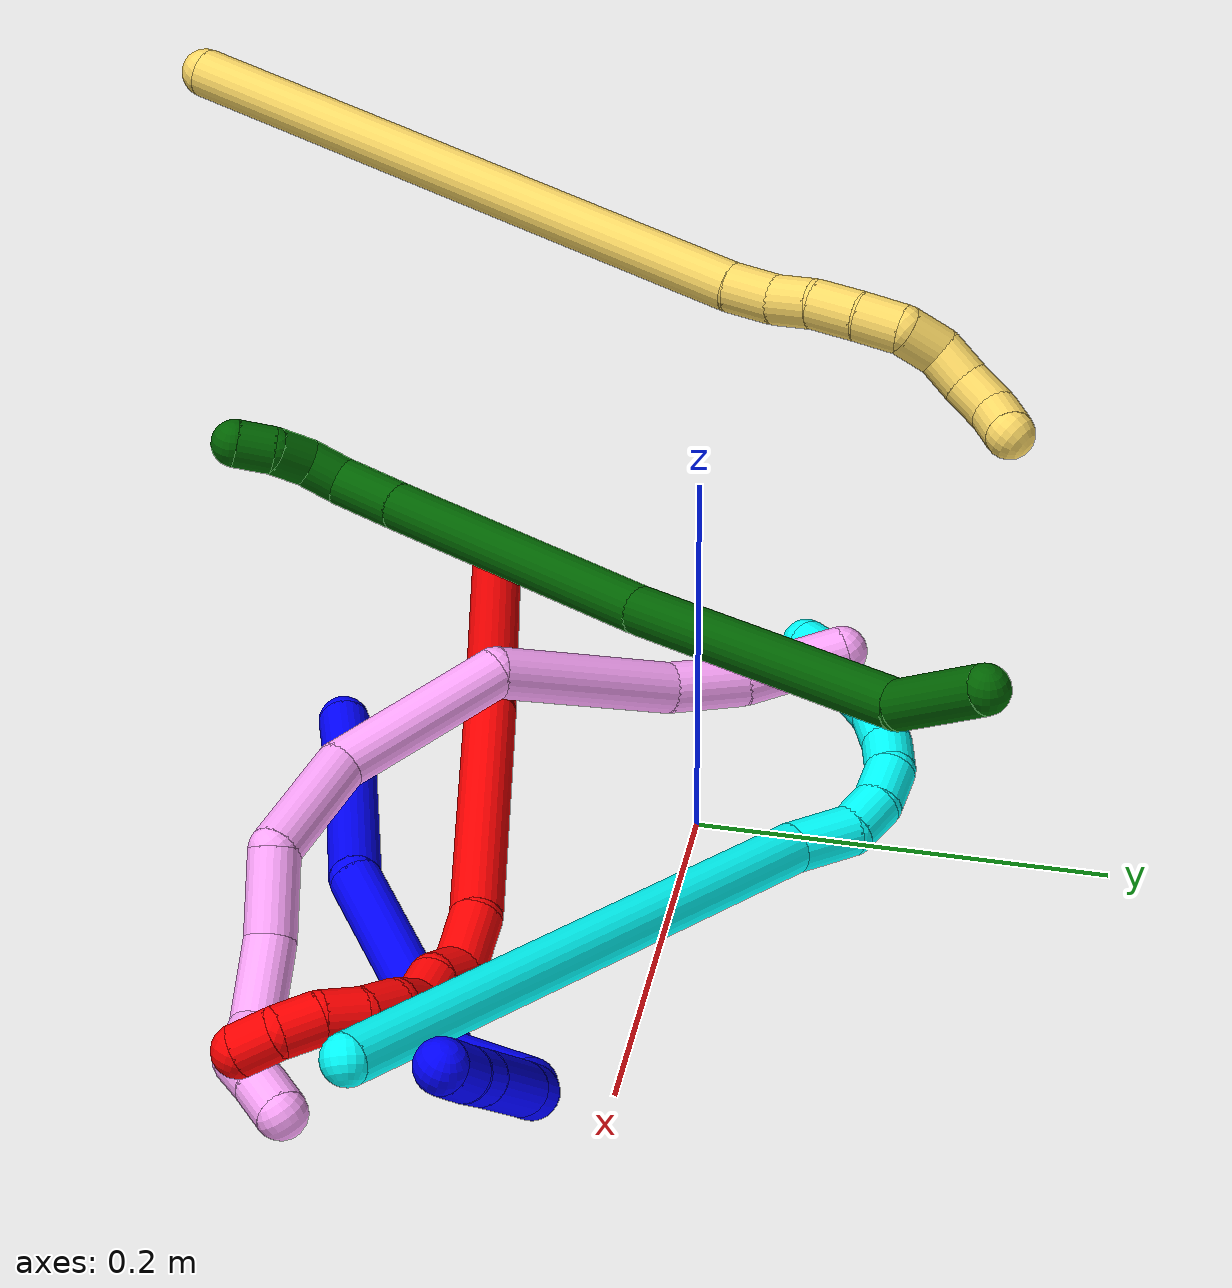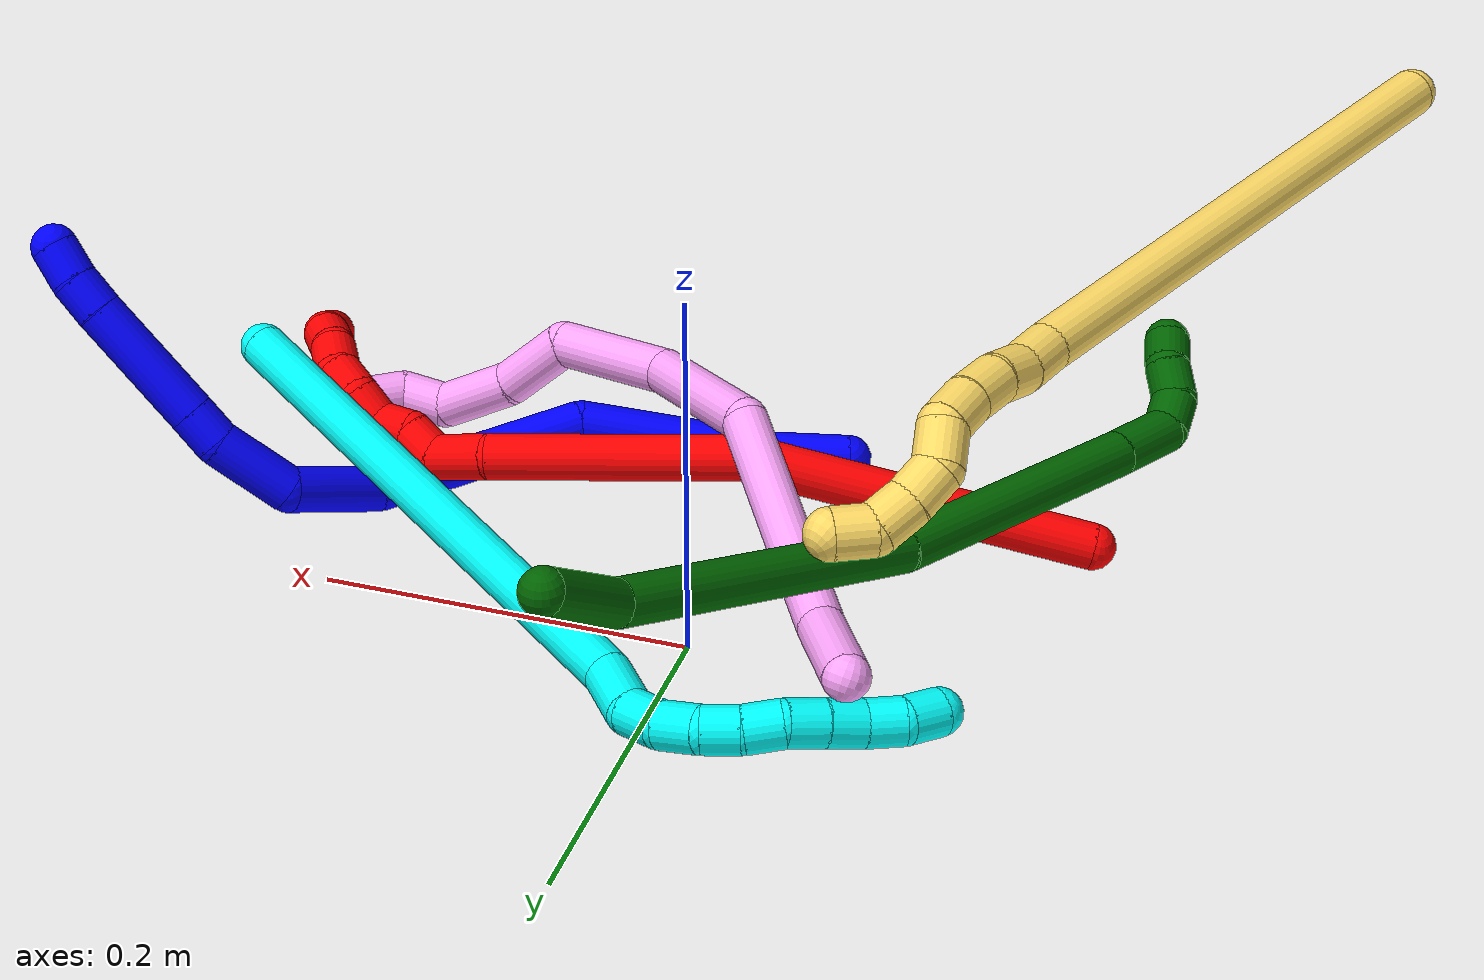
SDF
<sdf version="1.7">
 <world name="default">
  <plugin name="TubeGeneratorPlugin" filename="libtube_generator_plugin.so"/>
  <model name="photoneo_s_sensor">
   <static>1</static>
   <pose>0 0 2 1.57079 1.57079 3.14159</pose>
   <link name="link">
    <inertial><mass>0.1</mass></inertial>
    <sensor name="sensor" type="depth">
     <update_rate>30</update_rate>
     <camera>
      <horizontal_fov>1.22</horizontal_fov>
      <image><width>1920</width><height>1200</height><format>B8G8R8</format></image>
      <clip><near>0.1</near><far>4</far></clip>
      <depth_camera><output>points</output></depth_camera>
     </camera>
     <plugin name="camera_plugin" filename="libgazebo_ros_depth_camera.so">
      <baseline>0.2</baseline>
      <alwaysOn>1</alwaysOn>
      <updateRate>0.0</updateRate>
      <cameraName>camera_ir</cameraName>
      <imageTopicName>/camera/color/image_raw</imageTopicName>
      <cameraInfoTopicName>/camera/color/camera_info</cameraInfoTopicName>
      <depthImageTopicName>/camera/depth/image_raw</depthImageTopicName>
      <depthImageCameraInfoTopicName>/camera/depth/camera_info</depthImageCameraInfoTopicName>
      <pointCloudTopicName>/camera/depth/points</pointCloudTopicName>
      <frameName>fr_optical</frameName>
      <pointCloudCutoff>0.1</pointCloudCutoff>
      <pointCloudCutoffMax>2.0</pointCloudCutoffMax>
      <distortionK1>0</distortionK1>
      <distortionK2>0</distortionK2>
      <distortionK3>0</distortionK3>
      <distortionT1>0</distortionT1>
      <distortionT2>0</distortionT2>
      <CxPrime>0</CxPrime>
      <Cx>0</Cx>
      <Cy>0</Cy>
      <focalLength>0</focalLength>
      <hackBaseline>0</hackBaseline>
     </plugin>
    </sensor>
   </link>
  </model>
  <gravity>0 0 -9.8</gravity>
  <magnetic_field>6e-06 2.3e-05 -4.2e-05</magnetic_field>
  <atmosphere type="adiabatic"/>
  <physics name="default_physics" default="0" type="ode">
   <max_step_size>0.003</max_step_size>
   <real_time_factor>1</real_time_factor>
   <real_time_update_rate>1000</real_time_update_rate>
   <max_contacts>10000</max_contacts>
   <ode>
    <solver>
     <type>quick</type>
     <iters>100</iters>
     <sor>1.3</sor>
     <use_dynamic_moi_rescaling>0</use_dynamic_moi_rescaling>
    </solver>
    <constraints>
     <contact_max_correcting_vel>0</contact_max_correcting_vel>
     <contact_surface_layer>0.001</contact_surface_layer>
     <cfm>0</cfm>
     <erp>0.2</erp>
    </constraints>
   </ode>
  </physics>
  <scene><ambient>0.4 0.4 0.4 1</ambient><background>0.7 0.7 0.7 1</background><shadows>0</shadows></scene>
  <audio><device>default</device></audio>
  <spherical_coordinates>
   <surface_model>EARTH_WGS84</surface_model>
   <latitude_deg>0</latitude_deg>
   <longitude_deg>0</longitude_deg>
   <elevation>0</elevation>
   <heading_deg>0</heading_deg>
  </spherical_coordinates>
  <model name="bin">
   <static>1</static>
   <link name="bottom">
    <collision name="collision-bottom">
     <pose>0 0 -0.01 0 -0 0</pose>
     <geometry><box><size>0.8 0.6 0.02</size></box></geometry>
     <surface>
      <friction><ode><mu>100</mu><mu2>100</mu2></ode></friction>
      <contact><collide_bitmask>65535</collide_bitmask></contact>
     </surface>
    </collision>
   </link>
   <link name="west_wall">
    <collision name="collision-west_wall">
     <pose>-0.41 0 0.1 0 -0 0</pose>
     <geometry><box><size>0.02 0.6 0.2</size></box></geometry>
     <surface>
      <friction><ode><mu>100</mu><mu2>100</mu2></ode></friction>
      <contact><collide_bitmask>65535</collide_bitmask></contact>
     </surface>
    </collision>
   </link>
   <link name="east_wall">
    <collision name="collision-east_wall">
     <pose>0.41 0 0.1 0 -0 0</pose>
     <geometry><box><size>0.02 0.6 0.2</size></box></geometry>
     <surface>
      <friction><ode><mu>100</mu><mu2>100</mu2></ode></friction>
      <contact><collide_bitmask>65535</collide_bitmask></contact>
     </surface>
    </collision>
   </link>
   <link name="south_wall">
    <collision name="collision-south_wall">
     <pose>0 -0.31 0.1 0 -0 0</pose>
     <geometry><box><size>0.8 0.02 0.2</size></box></geometry>
     <surface>
      <friction><ode><mu>100</mu><mu2>100</mu2></ode></friction>
      <contact><collide_bitmask>65535</collide_bitmask></contact>
     </surface>
    </collision>
   </link>
   <link name="north_wall">
    <collision name="collision-north_wall">
     <pose>0 0.31 0.1 0 -0 0</pose>
     <geometry><box><size>0.8 0.02 0.2</size></box></geometry>
     <surface>
      <friction><ode><mu>100</mu><mu2>100</mu2></ode></friction>
      <contact><collide_bitmask>65535</collide_bitmask></contact>
     </surface>
    </collision>
   </link>
  </model>
  <model name="1">
   <static>0</static>
   <link name="1">
    <collision name="collision-cylinder-e_1_1_4">
     <pose>-0.00238 0.021508 -0.004459 -1.77522 -0.107921 0.132525</pose>
     <geometry><cylinder><radius>0.0125</radius><length>0.044189</length></cylinder></geometry>
     <surface>
      <friction><ode><mu>1.16</mu><mu2>1.16</mu2><slip1>0</slip1><slip2>0</slip2></ode></friction>
      <contact><ode><kp>1e+06</kp><kd>1</kd><max_vel>0</max_vel><min_depth>0.001</min_depth></ode></contact>
     </surface>
    </collision>
    <visual name="visual-cylinder-e_1_1_4">
     <pose>-0.00238 0.021508 -0.004459 -1.77522 -0.107921 0.132525</pose>
     <geometry><cylinder><radius>0.0125</radius><length>0.044189</length></cylinder></geometry>
     <material><ambient>0 0 1 1</ambient></material>
    </visual>
    <collision name="collision-cylinder-e_2_4_5">
     <pose>-0.014187 0.091891 -0.024054 -1.87111 -0.182208 0.246601</pose>
     <geometry><cylinder><radius>0.0125</radius><length>0.10405</length></cylinder></geometry>
     <surface>
      <friction><ode><mu>1.16</mu><mu2>1.16</mu2><slip1>0</slip1><slip2>0</slip2></ode></friction>
      <contact><ode><kp>1e+06</kp><kd>1</kd><max_vel>0</max_vel><min_depth>0.001</min_depth></ode></contact>
     </surface>
    </collision>
    <visual name="visual-cylinder-e_2_4_5">
     <pose>-0.014187 0.091891 -0.024054 -1.87111 -0.182208 0.246601</pose>
     <geometry><cylinder><radius>0.0125</radius><length>0.10405</length></cylinder></geometry>
     <material><ambient>0 0 1 1</ambient></material>
    </visual>
    <collision name="collision-cylinder-e_3_5_6">
     <pose>-0.009573 0.197122 -0.041988 -1.62042 0.243876 -0.256157</pose>
     <geometry><cylinder><radius>0.0125</radius><length>0.116296</length></cylinder></geometry>
     <surface>
      <friction><ode><mu>1.16</mu><mu2>1.16</mu2><slip1>0</slip1><slip2>0</slip2></ode></friction>
      <contact><ode><kp>1e+06</kp><kd>1</kd><max_vel>0</max_vel><min_depth>0.001</min_depth></ode></contact>
     </surface>
    </collision>
    <visual name="visual-cylinder-e_3_5_6">
     <pose>-0.009573 0.197122 -0.041988 -1.62042 0.243876 -0.256157</pose>
     <geometry><cylinder><radius>0.0125</radius><length>0.116296</length></cylinder></geometry>
     <material><ambient>0 0 1 1</ambient></material>
    </visual>
    <collision name="collision-cylinder-e_4_6_7">
     <pose>0.015241 0.274272 -0.061115 -2.23649 0.386972 -0.766164</pose>
     <geometry><cylinder><radius>0.0125</radius><length>0.057095</length></cylinder></geometry>
     <surface>
      <friction><ode><mu>1.16</mu><mu2>1.16</mu2><slip1>0</slip1><slip2>0</slip2></ode></friction>
      <contact><ode><kp>1e+06</kp><kd>1</kd><max_vel>0</max_vel><min_depth>0.001</min_depth></ode></contact>
     </surface>
    </collision>
    <visual name="visual-cylinder-e_4_6_7">
     <pose>0.015241 0.274272 -0.061115 -2.23649 0.386972 -0.766164</pose>
     <geometry><cylinder><radius>0.0125</radius><length>0.057095</length></cylinder></geometry>
     <material><ambient>0 0 1 1</ambient></material>
    </visual>
    <collision name="collision-cylinder-e_5_7_8">
     <pose>0.019731 0.310291 -0.092997 -2.36685 -0.281018 0.667428</pose>
     <geometry><cylinder><radius>0.0125</radius><length>0.045312</length></cylinder></geometry>
     <surface>
      <friction><ode><mu>1.16</mu><mu2>1.16</mu2><slip1>0</slip1><slip2>0</slip2></ode></friction>
      <contact><ode><kp>1e+06</kp><kd>1</kd><max_vel>0</max_vel><min_depth>0.001</min_depth></ode></contact>
     </surface>
    </collision>
    <visual name="visual-cylinder-e_5_7_8">
     <pose>0.019731 0.310291 -0.092997 -2.36685 -0.281018 0.667428</pose>
     <geometry><cylinder><radius>0.0125</radius><length>0.045312</length></cylinder></geometry>
     <material><ambient>0 0 1 1</ambient></material>
    </visual>
    <collision name="collision-cylinder-e_6_8_9">
     <pose>0.008149 0.33067 -0.115786 -2.52278 -0.537964 1.42322</pose>
     <geometry><cylinder><radius>0.0125</radius><length>0.020685</length></cylinder></geometry>
     <surface>
      <friction><ode><mu>1.16</mu><mu2>1.16</mu2><slip1>0</slip1><slip2>0</slip2></ode></friction>
      <contact><ode><kp>1e+06</kp><kd>1</kd><max_vel>0</max_vel><min_depth>0.001</min_depth></ode></contact>
     </surface>
    </collision>
    <visual name="visual-cylinder-e_6_8_9">
     <pose>0.008149 0.33067 -0.115786 -2.52278 -0.537964 1.42322</pose>
     <geometry><cylinder><radius>0.0125</radius><length>0.020685</length></cylinder></geometry>
     <material><ambient>0 0 1 1</ambient></material>
    </visual>
    <collision name="collision-cylinder-e_7_9_10">
     <pose>-0.01538 0.354016 -0.147568 -2.50375 -0.537934 1.39121</pose>
     <geometry><cylinder><radius>0.0125</radius><length>0.07116</length></cylinder></geometry>
     <surface>
      <friction><ode><mu>1.16</mu><mu2>1.16</mu2><slip1>0</slip1><slip2>0</slip2></ode></friction>
      <contact><ode><kp>1e+06</kp><kd>1</kd><max_vel>0</max_vel><min_depth>0.001</min_depth></ode></contact>
     </surface>
    </collision>
    <visual name="visual-cylinder-e_7_9_10">
     <pose>-0.01538 0.354016 -0.147568 -2.50375 -0.537934 1.39121</pose>
     <geometry><cylinder><radius>0.0125</radius><length>0.07116</length></cylinder></geometry>
     <material><ambient>0 0 1 1</ambient></material>
    </visual>
    <collision name="collision-cylinder-e_8_10_11">
     <pose>-0.039534 0.377188 -0.178952 -2.51221 -0.611106 1.53935</pose>
     <geometry><cylinder><radius>0.0125</radius><length>0.02065</length></cylinder></geometry>
     <surface>
      <friction><ode><mu>1.16</mu><mu2>1.16</mu2><slip1>0</slip1><slip2>0</slip2></ode></friction>
      <contact><ode><kp>1e+06</kp><kd>1</kd><max_vel>0</max_vel><min_depth>0.001</min_depth></ode></contact>
     </surface>
    </collision>
    <visual name="visual-cylinder-e_8_10_11">
     <pose>-0.039534 0.377188 -0.178952 -2.51221 -0.611106 1.53935</pose>
     <geometry><cylinder><radius>0.0125</radius><length>0.02065</length></cylinder></geometry>
     <material><ambient>0 0 1 1</ambient></material>
    </visual>
    <collision name="collision-cylinder-e_9_11_2">
     <pose>-0.052474 0.385891 -0.192317 -2.62319 -0.750873 1.95713</pose>
     <geometry><cylinder><radius>0.0125</radius><length>0.020564</length></cylinder></geometry>
     <surface>
      <friction><ode><mu>1.16</mu><mu2>1.16</mu2><slip1>0</slip1><slip2>0</slip2></ode></friction>
      <contact><ode><kp>1e+06</kp><kd>1</kd><max_vel>0</max_vel><min_depth>0.001</min_depth></ode></contact>
     </surface>
    </collision>
    <visual name="visual-cylinder-e_9_11_2">
     <pose>-0.052474 0.385891 -0.192317 -2.62319 -0.750873 1.95713</pose>
     <geometry><cylinder><radius>0.0125</radius><length>0.020564</length></cylinder></geometry>
     <material><ambient>0 0 1 1</ambient></material>
    </visual>
    <collision name="collision-sphere-2">
     <pose>-0.059489 0.389616 -0.198847 0 -0 0</pose>
     <geometry><sphere><radius>0.0125</radius></sphere></geometry>
     <surface>
      <friction><ode><mu>1.16</mu><mu2>1.16</mu2><slip1>0</slip1><slip2>0</slip2></ode></friction>
      <contact><ode><kp>1e+06</kp><kd>1</kd><max_vel>0</max_vel><min_depth>0.001</min_depth></ode></contact>
     </surface>
    </collision>
    <visual name="visual-sphere-2">
     <pose>-0.059489 0.389616 -0.198847 0 -0 0</pose>
     <geometry><sphere><radius>0.0125</radius></sphere></geometry>
     <material><ambient>0 0 1 1</ambient></material>
    </visual>
    <collision name="collision-sphere-11">
     <pose>-0.045459 0.382166 -0.185788 0 -0 0</pose>
     <geometry><sphere><radius>0.0125</radius></sphere></geometry>
     <surface>
      <friction><ode><mu>1.16</mu><mu2>1.16</mu2><slip1>0</slip1><slip2>0</slip2></ode></friction>
      <contact><ode><kp>1e+06</kp><kd>1</kd><max_vel>0</max_vel><min_depth>0.001</min_depth></ode></contact>
     </surface>
    </collision>
    <visual name="visual-sphere-11">
     <pose>-0.045459 0.382166 -0.185788 0 -0 0</pose>
     <geometry><sphere><radius>0.0125</radius></sphere></geometry>
     <material><ambient>0 0 1 1</ambient></material>
    </visual>
    <collision name="collision-sphere-10">
     <pose>-0.03361 0.372211 -0.172116 0 -0 0</pose>
     <geometry><sphere><radius>0.0125</radius></sphere></geometry>
     <surface>
      <friction><ode><mu>1.16</mu><mu2>1.16</mu2><slip1>0</slip1><slip2>0</slip2></ode></friction>
      <contact><ode><kp>1e+06</kp><kd>1</kd><max_vel>0</max_vel><min_depth>0.001</min_depth></ode></contact>
     </surface>
    </collision>
    <visual name="visual-sphere-10">
     <pose>-0.03361 0.372211 -0.172116 0 -0 0</pose>
     <geometry><sphere><radius>0.0125</radius></sphere></geometry>
     <material><ambient>0 0 1 1</ambient></material>
    </visual>
    <collision name="collision-sphere-9">
     <pose>0.002849 0.335822 -0.123021 0 -0 0</pose>
     <geometry><sphere><radius>0.0125</radius></sphere></geometry>
     <surface>
      <friction><ode><mu>1.16</mu><mu2>1.16</mu2><slip1>0</slip1><slip2>0</slip2></ode></friction>
      <contact><ode><kp>1e+06</kp><kd>1</kd><max_vel>0</max_vel><min_depth>0.001</min_depth></ode></contact>
     </surface>
    </collision>
    <visual name="visual-sphere-9">
     <pose>0.002849 0.335822 -0.123021 0 -0 0</pose>
     <geometry><sphere><radius>0.0125</radius></sphere></geometry>
     <material><ambient>0 0 1 1</ambient></material>
    </visual>
    <collision name="collision-sphere-4">
     <pose>-0.00476 0.043017 -0.008918 0 -0 0</pose>
     <geometry><sphere><radius>0.0125</radius></sphere></geometry>
     <surface>
      <friction><ode><mu>1.16</mu><mu2>1.16</mu2><slip1>0</slip1><slip2>0</slip2></ode></friction>
      <contact><ode><kp>1e+06</kp><kd>1</kd><max_vel>0</max_vel><min_depth>0.001</min_depth></ode></contact>
     </surface>
    </collision>
    <visual name="visual-sphere-4">
     <pose>-0.00476 0.043017 -0.008918 0 -0 0</pose>
     <geometry><sphere><radius>0.0125</radius></sphere></geometry>
     <material><ambient>0 0 1 1</ambient></material>
    </visual>
    <collision name="collision-sphere-1">
     <geometry><sphere><radius>0.0125</radius></sphere></geometry>
     <surface>
      <friction><ode><mu>1.16</mu><mu2>1.16</mu2><slip1>0</slip1><slip2>0</slip2></ode></friction>
      <contact><ode><kp>1e+06</kp><kd>1</kd><max_vel>0</max_vel><min_depth>0.001</min_depth></ode></contact>
     </surface>
    </collision>
    <visual name="visual-sphere-1">
     <geometry><sphere><radius>0.0125</radius></sphere></geometry>
     <material><ambient>0 0 1 1</ambient></material>
    </visual>
    <collision name="collision-sphere-8">
     <pose>0.013448 0.325518 -0.108552 0 -0 0</pose>
     <geometry><sphere><radius>0.0125</radius></sphere></geometry>
     <surface>
      <friction><ode><mu>1.16</mu><mu2>1.16</mu2><slip1>0</slip1><slip2>0</slip2></ode></friction>
      <contact><ode><kp>1e+06</kp><kd>1</kd><max_vel>0</max_vel><min_depth>0.001</min_depth></ode></contact>
     </surface>
    </collision>
    <visual name="visual-sphere-8">
     <pose>0.013448 0.325518 -0.108552 0 -0 0</pose>
     <geometry><sphere><radius>0.0125</radius></sphere></geometry>
     <material><ambient>0 0 1 1</ambient></material>
    </visual>
    <collision name="collision-sphere-5">
     <pose>-0.023614 0.140764 -0.039189 0 -0 0</pose>
     <geometry><sphere><radius>0.0125</radius></sphere></geometry>
     <surface>
      <friction><ode><mu>1.16</mu><mu2>1.16</mu2><slip1>0</slip1><slip2>0</slip2></ode></friction>
      <contact><ode><kp>1e+06</kp><kd>1</kd><max_vel>0</max_vel><min_depth>0.001</min_depth></ode></contact>
     </surface>
    </collision>
    <visual name="visual-sphere-5">
     <pose>-0.023614 0.140764 -0.039189 0 -0 0</pose>
     <geometry><sphere><radius>0.0125</radius></sphere></geometry>
     <material><ambient>0 0 1 1</ambient></material>
    </visual>
    <collision name="collision-sphere-6">
     <pose>0.004468 0.25348 -0.044787 0 -0 0</pose>
     <geometry><sphere><radius>0.0125</radius></sphere></geometry>
     <surface>
      <friction><ode><mu>1.16</mu><mu2>1.16</mu2><slip1>0</slip1><slip2>0</slip2></ode></friction>
      <contact><ode><kp>1e+06</kp><kd>1</kd><max_vel>0</max_vel><min_depth>0.001</min_depth></ode></contact>
     </surface>
    </collision>
    <visual name="visual-sphere-6">
     <pose>0.004468 0.25348 -0.044787 0 -0 0</pose>
     <geometry><sphere><radius>0.0125</radius></sphere></geometry>
     <material><ambient>0 0 1 1</ambient></material>
    </visual>
    <collision name="collision-sphere-7">
     <pose>0.026015 0.295064 -0.077442 0 -0 0</pose>
     <geometry><sphere><radius>0.0125</radius></sphere></geometry>
     <surface>
      <friction><ode><mu>1.16</mu><mu2>1.16</mu2><slip1>0</slip1><slip2>0</slip2></ode></friction>
      <contact><ode><kp>1e+06</kp><kd>1</kd><max_vel>0</max_vel><min_depth>0.001</min_depth></ode></contact>
     </surface>
    </collision>
    <visual name="visual-sphere-7">
     <pose>0.026015 0.295064 -0.077442 0 -0 0</pose>
     <geometry><sphere><radius>0.0125</radius></sphere></geometry>
     <material><ambient>0 0 1 1</ambient></material>
    </visual>
    <inertial>
     <pose>-0.007503 0.221823 -0.071665 0 -0 0</pose>
     <mass>0.5</mass>
     <inertia>
      <ixx>0.000266</ixx>
      <ixy>0</ixy>
      <ixz>0</ixz>
      <iyy>2.2e-05</iyy>
      <iyz>0</iyz>
      <izz>-0.000284</izz>
     </inertia>
    </inertial>
   </link>
   <pose>-0.030825 -0.183024 0.01248 -2.96751 0.236803 1.98887</pose>
  </model>
  <model name="2">
   <static>0</static>
   <link name="2">
    <collision name="collision-cylinder-e_1_1_4">
     <pose>0.084731 0.038203 -0.011958 -1.87414 1.12943 -1.42301</pose>
     <geometry><cylinder><radius>0.0125</radius><length>0.187423</length></cylinder></geometry>
     <surface>
      <friction><ode><mu>1.16</mu><mu2>1.16</mu2><slip1>0</slip1><slip2>0</slip2></ode></friction>
      <contact><ode><kp>1e+06</kp><kd>1</kd><max_vel>0</max_vel><min_depth>0.001</min_depth></ode></contact>
     </surface>
    </collision>
    <visual name="visual-cylinder-e_1_1_4">
     <pose>0.084731 0.038203 -0.011958 -1.87414 1.12943 -1.42301</pose>
     <geometry><cylinder><radius>0.0125</radius><length>0.187423</length></cylinder></geometry>
     <material><ambient>1 0 0 1</ambient></material>
    </visual>
    <collision name="collision-cylinder-e_2_4_5">
     <pose>0.225444 0.107104 -0.053192 -2.33252 0.922359 -1.71919</pose>
     <geometry><cylinder><radius>0.0125</radius><length>0.140477</length></cylinder></geometry>
     <surface>
      <friction><ode><mu>1.16</mu><mu2>1.16</mu2><slip1>0</slip1><slip2>0</slip2></ode></friction>
      <contact><ode><kp>1e+06</kp><kd>1</kd><max_vel>0</max_vel><min_depth>0.001</min_depth></ode></contact>
     </surface>
    </collision>
    <visual name="visual-cylinder-e_2_4_5">
     <pose>0.225444 0.107104 -0.053192 -2.33252 0.922359 -1.71919</pose>
     <geometry><cylinder><radius>0.0125</radius><length>0.140477</length></cylinder></geometry>
     <material><ambient>1 0 0 1</ambient></material>
    </visual>
    <collision name="collision-cylinder-e_3_5_6">
     <pose>0.293658 0.141848 -0.092002 -2.74013 0.868178 -2.3144</pose>
     <geometry><cylinder><radius>0.0125</radius><length>0.032054</length></cylinder></geometry>
     <surface>
      <friction><ode><mu>1.16</mu><mu2>1.16</mu2><slip1>0</slip1><slip2>0</slip2></ode></friction>
      <contact><ode><kp>1e+06</kp><kd>1</kd><max_vel>0</max_vel><min_depth>0.001</min_depth></ode></contact>
     </surface>
    </collision>
    <visual name="visual-cylinder-e_3_5_6">
     <pose>0.293658 0.141848 -0.092002 -2.74013 0.868178 -2.3144</pose>
     <geometry><cylinder><radius>0.0125</radius><length>0.032054</length></cylinder></geometry>
     <material><ambient>1 0 0 1</ambient></material>
    </visual>
    <collision name="collision-cylinder-e_4_6_7">
     <pose>0.315685 0.144017 -0.102328 1.96987 1.36562 1.77288</pose>
     <geometry><cylinder><radius>0.0125</radius><length>0.020012</length></cylinder></geometry>
     <surface>
      <friction><ode><mu>1.16</mu><mu2>1.16</mu2><slip1>0</slip1><slip2>0</slip2></ode></friction>
      <contact><ode><kp>1e+06</kp><kd>1</kd><max_vel>0</max_vel><min_depth>0.001</min_depth></ode></contact>
     </surface>
    </collision>
    <visual name="visual-cylinder-e_4_6_7">
     <pose>0.315685 0.144017 -0.102328 1.96987 1.36562 1.77288</pose>
     <geometry><cylinder><radius>0.0125</radius><length>0.020012</length></cylinder></geometry>
     <material><ambient>1 0 0 1</ambient></material>
    </visual>
    <collision name="collision-cylinder-e_5_7_8">
     <pose>0.33455 0.143402 -0.107142 -2.83715 1.13567 -2.66959</pose>
     <geometry><cylinder><radius>0.0125</radius><length>0.020001</length></cylinder></geometry>
     <surface>
      <friction><ode><mu>1.16</mu><mu2>1.16</mu2><slip1>0</slip1><slip2>0</slip2></ode></friction>
      <contact><ode><kp>1e+06</kp><kd>1</kd><max_vel>0</max_vel><min_depth>0.001</min_depth></ode></contact>
     </surface>
    </collision>
    <visual name="visual-cylinder-e_5_7_8">
     <pose>0.33455 0.143402 -0.107142 -2.83715 1.13567 -2.66959</pose>
     <geometry><cylinder><radius>0.0125</radius><length>0.020001</length></cylinder></geometry>
     <material><ambient>1 0 0 1</ambient></material>
    </visual>
    <collision name="collision-cylinder-e_6_8_9">
     <pose>0.353323 0.142687 -0.109727 0.94269 1.32401 0.756159</pose>
     <geometry><cylinder><radius>0.0125</radius><length>0.020014</length></cylinder></geometry>
     <surface>
      <friction><ode><mu>1.16</mu><mu2>1.16</mu2><slip1>0</slip1><slip2>0</slip2></ode></friction>
      <contact><ode><kp>1e+06</kp><kd>1</kd><max_vel>0</max_vel><min_depth>0.001</min_depth></ode></contact>
     </surface>
    </collision>
    <visual name="visual-cylinder-e_6_8_9">
     <pose>0.353323 0.142687 -0.109727 0.94269 1.32401 0.756159</pose>
     <geometry><cylinder><radius>0.0125</radius><length>0.020014</length></cylinder></geometry>
     <material><ambient>1 0 0 1</ambient></material>
    </visual>
    <collision name="collision-cylinder-e_7_9_10">
     <pose>0.372123 0.136984 -0.110145 2.03264 1.14172 1.6071</pose>
     <geometry><cylinder><radius>0.0125</radius><length>0.020006</length></cylinder></geometry>
     <surface>
      <friction><ode><mu>1.16</mu><mu2>1.16</mu2><slip1>0</slip1><slip2>0</slip2></ode></friction>
      <contact><ode><kp>1e+06</kp><kd>1</kd><max_vel>0</max_vel><min_depth>0.001</min_depth></ode></contact>
     </surface>
    </collision>
    <visual name="visual-cylinder-e_7_9_10">
     <pose>0.372123 0.136984 -0.110145 2.03264 1.14172 1.6071</pose>
     <geometry><cylinder><radius>0.0125</radius><length>0.020006</length></cylinder></geometry>
     <material><ambient>1 0 0 1</ambient></material>
    </visual>
    <collision name="collision-cylinder-e_8_10_11">
     <pose>0.387956 0.126293 -0.114494 1.91472 0.738662 1.0054</pose>
     <geometry><cylinder><radius>0.0125</radius><length>0.020012</length></cylinder></geometry>
     <surface>
      <friction><ode><mu>1.16</mu><mu2>1.16</mu2><slip1>0</slip1><slip2>0</slip2></ode></friction>
      <contact><ode><kp>1e+06</kp><kd>1</kd><max_vel>0</max_vel><min_depth>0.001</min_depth></ode></contact>
     </surface>
    </collision>
    <visual name="visual-cylinder-e_8_10_11">
     <pose>0.387956 0.126293 -0.114494 1.91472 0.738662 1.0054</pose>
     <geometry><cylinder><radius>0.0125</radius><length>0.020012</length></cylinder></geometry>
     <material><ambient>1 0 0 1</ambient></material>
    </visual>
    <collision name="collision-cylinder-e_9_11_12">
     <pose>0.400724 0.11324 -0.122142 2.27319 0.647355 1.25258</pose>
     <geometry><cylinder><radius>0.0125</radius><length>0.02</length></cylinder></geometry>
     <surface>
      <friction><ode><mu>1.16</mu><mu2>1.16</mu2><slip1>0</slip1><slip2>0</slip2></ode></friction>
      <contact><ode><kp>1e+06</kp><kd>1</kd><max_vel>0</max_vel><min_depth>0.001</min_depth></ode></contact>
     </surface>
    </collision>
    <visual name="visual-cylinder-e_9_11_12">
     <pose>0.400724 0.11324 -0.122142 2.27319 0.647355 1.25258</pose>
     <geometry><cylinder><radius>0.0125</radius><length>0.02</length></cylinder></geometry>
     <material><ambient>1 0 0 1</ambient></material>
    </visual>
    <collision name="collision-cylinder-e_10_12_2">
     <pose>0.408236 0.100374 -0.134497 2.38661 0.148704 0.3714</pose>
     <geometry><cylinder><radius>0.0125</radius><length>0.02</length></cylinder></geometry>
     <surface>
      <friction><ode><mu>1.16</mu><mu2>1.16</mu2><slip1>0</slip1><slip2>0</slip2></ode></friction>
      <contact><ode><kp>1e+06</kp><kd>1</kd><max_vel>0</max_vel><min_depth>0.001</min_depth></ode></contact>
     </surface>
    </collision>
    <visual name="visual-cylinder-e_10_12_2">
     <pose>0.408236 0.100374 -0.134497 2.38661 0.148704 0.3714</pose>
     <geometry><cylinder><radius>0.0125</radius><length>0.02</length></cylinder></geometry>
     <material><ambient>1 0 0 1</ambient></material>
    </visual>
    <collision name="collision-sphere-2">
     <pose>0.409718 0.093597 -0.1417 0 -0 0</pose>
     <geometry><sphere><radius>0.0125</radius></sphere></geometry>
     <surface>
      <friction><ode><mu>1.16</mu><mu2>1.16</mu2><slip1>0</slip1><slip2>0</slip2></ode></friction>
      <contact><ode><kp>1e+06</kp><kd>1</kd><max_vel>0</max_vel><min_depth>0.001</min_depth></ode></contact>
     </surface>
    </collision>
    <visual name="visual-sphere-2">
     <pose>0.409718 0.093597 -0.1417 0 -0 0</pose>
     <geometry><sphere><radius>0.0125</radius></sphere></geometry>
     <material><ambient>1 0 0 1</ambient></material>
    </visual>
    <collision name="collision-sphere-12">
     <pose>0.406755 0.107151 -0.127295 0 -0 0</pose>
     <geometry><sphere><radius>0.0125</radius></sphere></geometry>
     <surface>
      <friction><ode><mu>1.16</mu><mu2>1.16</mu2><slip1>0</slip1><slip2>0</slip2></ode></friction>
      <contact><ode><kp>1e+06</kp><kd>1</kd><max_vel>0</max_vel><min_depth>0.001</min_depth></ode></contact>
     </surface>
    </collision>
    <visual name="visual-sphere-12">
     <pose>0.406755 0.107151 -0.127295 0 -0 0</pose>
     <geometry><sphere><radius>0.0125</radius></sphere></geometry>
     <material><ambient>1 0 0 1</ambient></material>
    </visual>
    <collision name="collision-sphere-11">
     <pose>0.394693 0.119329 -0.116988 0 -0 0</pose>
     <geometry><sphere><radius>0.0125</radius></sphere></geometry>
     <surface>
      <friction><ode><mu>1.16</mu><mu2>1.16</mu2><slip1>0</slip1><slip2>0</slip2></ode></friction>
      <contact><ode><kp>1e+06</kp><kd>1</kd><max_vel>0</max_vel><min_depth>0.001</min_depth></ode></contact>
     </surface>
    </collision>
    <visual name="visual-sphere-11">
     <pose>0.394693 0.119329 -0.116988 0 -0 0</pose>
     <geometry><sphere><radius>0.0125</radius></sphere></geometry>
     <material><ambient>1 0 0 1</ambient></material>
    </visual>
    <collision name="collision-sphere-10">
     <pose>0.381219 0.133258 -0.111999 0 -0 0</pose>
     <geometry><sphere><radius>0.0125</radius></sphere></geometry>
     <surface>
      <friction><ode><mu>1.16</mu><mu2>1.16</mu2><slip1>0</slip1><slip2>0</slip2></ode></friction>
      <contact><ode><kp>1e+06</kp><kd>1</kd><max_vel>0</max_vel><min_depth>0.001</min_depth></ode></contact>
     </surface>
    </collision>
    <visual name="visual-sphere-10">
     <pose>0.381219 0.133258 -0.111999 0 -0 0</pose>
     <geometry><sphere><radius>0.0125</radius></sphere></geometry>
     <material><ambient>1 0 0 1</ambient></material>
    </visual>
    <collision name="collision-sphere-9">
     <pose>0.363027 0.140709 -0.10829 0 -0 0</pose>
     <geometry><sphere><radius>0.0125</radius></sphere></geometry>
     <surface>
      <friction><ode><mu>1.16</mu><mu2>1.16</mu2><slip1>0</slip1><slip2>0</slip2></ode></friction>
      <contact><ode><kp>1e+06</kp><kd>1</kd><max_vel>0</max_vel><min_depth>0.001</min_depth></ode></contact>
     </surface>
    </collision>
    <visual name="visual-sphere-9">
     <pose>0.363027 0.140709 -0.10829 0 -0 0</pose>
     <geometry><sphere><radius>0.0125</radius></sphere></geometry>
     <material><ambient>1 0 0 1</ambient></material>
    </visual>
    <collision name="collision-sphere-4">
     <pose>0.169462 0.076406 -0.023915 0 -0 0</pose>
     <geometry><sphere><radius>0.0125</radius></sphere></geometry>
     <surface>
      <friction><ode><mu>1.16</mu><mu2>1.16</mu2><slip1>0</slip1><slip2>0</slip2></ode></friction>
      <contact><ode><kp>1e+06</kp><kd>1</kd><max_vel>0</max_vel><min_depth>0.001</min_depth></ode></contact>
     </surface>
    </collision>
    <visual name="visual-sphere-4">
     <pose>0.169462 0.076406 -0.023915 0 -0 0</pose>
     <geometry><sphere><radius>0.0125</radius></sphere></geometry>
     <material><ambient>1 0 0 1</ambient></material>
    </visual>
    <collision name="collision-sphere-1">
     <geometry><sphere><radius>0.0125</radius></sphere></geometry>
     <surface>
      <friction><ode><mu>1.16</mu><mu2>1.16</mu2><slip1>0</slip1><slip2>0</slip2></ode></friction>
      <contact><ode><kp>1e+06</kp><kd>1</kd><max_vel>0</max_vel><min_depth>0.001</min_depth></ode></contact>
     </surface>
    </collision>
    <visual name="visual-sphere-1">
     <geometry><sphere><radius>0.0125</radius></sphere></geometry>
     <material><ambient>1 0 0 1</ambient></material>
    </visual>
    <collision name="collision-sphere-8">
     <pose>0.343619 0.144666 -0.111163 0 -0 0</pose>
     <geometry><sphere><radius>0.0125</radius></sphere></geometry>
     <surface>
      <friction><ode><mu>1.16</mu><mu2>1.16</mu2><slip1>0</slip1><slip2>0</slip2></ode></friction>
      <contact><ode><kp>1e+06</kp><kd>1</kd><max_vel>0</max_vel><min_depth>0.001</min_depth></ode></contact>
     </surface>
    </collision>
    <visual name="visual-sphere-8">
     <pose>0.343619 0.144666 -0.111163 0 -0 0</pose>
     <geometry><sphere><radius>0.0125</radius></sphere></geometry>
     <material><ambient>1 0 0 1</ambient></material>
    </visual>
    <collision name="collision-sphere-5">
     <pose>0.281427 0.137801 -0.082469 0 -0 0</pose>
     <geometry><sphere><radius>0.0125</radius></sphere></geometry>
     <surface>
      <friction><ode><mu>1.16</mu><mu2>1.16</mu2><slip1>0</slip1><slip2>0</slip2></ode></friction>
      <contact><ode><kp>1e+06</kp><kd>1</kd><max_vel>0</max_vel><min_depth>0.001</min_depth></ode></contact>
     </surface>
    </collision>
    <visual name="visual-sphere-5">
     <pose>0.281427 0.137801 -0.082469 0 -0 0</pose>
     <geometry><sphere><radius>0.0125</radius></sphere></geometry>
     <material><ambient>1 0 0 1</ambient></material>
    </visual>
    <collision name="collision-sphere-6">
     <pose>0.305889 0.145895 -0.101536 0 -0 0</pose>
     <geometry><sphere><radius>0.0125</radius></sphere></geometry>
     <surface>
      <friction><ode><mu>1.16</mu><mu2>1.16</mu2><slip1>0</slip1><slip2>0</slip2></ode></friction>
      <contact><ode><kp>1e+06</kp><kd>1</kd><max_vel>0</max_vel><min_depth>0.001</min_depth></ode></contact>
     </surface>
    </collision>
    <visual name="visual-sphere-6">
     <pose>0.305889 0.145895 -0.101536 0 -0 0</pose>
     <geometry><sphere><radius>0.0125</radius></sphere></geometry>
     <material><ambient>1 0 0 1</ambient></material>
    </visual>
    <collision name="collision-sphere-7">
     <pose>0.325481 0.142138 -0.10312 0 -0 0</pose>
     <geometry><sphere><radius>0.0125</radius></sphere></geometry>
     <surface>
      <friction><ode><mu>1.16</mu><mu2>1.16</mu2><slip1>0</slip1><slip2>0</slip2></ode></friction>
      <contact><ode><kp>1e+06</kp><kd>1</kd><max_vel>0</max_vel><min_depth>0.001</min_depth></ode></contact>
     </surface>
    </collision>
    <visual name="visual-sphere-7">
     <pose>0.325481 0.142138 -0.10312 0 -0 0</pose>
     <geometry><sphere><radius>0.0125</radius></sphere></geometry>
     <material><ambient>1 0 0 1</ambient></material>
    </visual>
    <inertial>
     <pose>0.216863 0.089798 -0.057354 0 -0 0</pose>
     <mass>0.5</mass>
     <inertia>
      <ixx>-0.000329</ixx>
      <ixy>0</ixy>
      <ixz>0</ixz>
      <iyy>0.00025</iyy>
      <iyz>0</iyz>
      <izz>-0.00104</izz>
     </inertia>
    </inertial>
   </link>
   <pose>-0.177933 -0.13883 0.011492 -0.174406 -0.461201 -0.193602</pose>
  </model>
  <model name="3">
   <static>0</static>
   <link name="3">
    <collision name="collision-cylinder-e_1_1_4">
     <pose>-0.118522 0.076744 0.053613 -0.961011 -0.902266 0.494704</pose>
     <geometry><cylinder><radius>0.0125</radius><length>0.302068</length></cylinder></geometry>
     <surface>
      <friction><ode><mu>1.16</mu><mu2>1.16</mu2><slip1>0</slip1><slip2>0</slip2></ode></friction>
      <contact><ode><kp>1e+06</kp><kd>1</kd><max_vel>0</max_vel><min_depth>0.001</min_depth></ode></contact>
     </surface>
    </collision>
    <visual name="visual-cylinder-e_1_1_4">
     <pose>-0.118522 0.076744 0.053613 -0.961011 -0.902266 0.494704</pose>
     <geometry><cylinder><radius>0.0125</radius><length>0.302068</length></cylinder></geometry>
     <material><ambient>0.003922 1 0.996078 1</ambient></material>
    </visual>
    <collision name="collision-cylinder-e_2_4_5">
     <pose>-0.246491 0.166275 0.111318 -1.26112 -0.613191 0.454213</pose>
     <geometry><cylinder><radius>0.0125</radius><length>0.032833</length></cylinder></geometry>
     <surface>
      <friction><ode><mu>1.16</mu><mu2>1.16</mu2><slip1>0</slip1><slip2>0</slip2></ode></friction>
      <contact><ode><kp>1e+06</kp><kd>1</kd><max_vel>0</max_vel><min_depth>0.001</min_depth></ode></contact>
     </surface>
    </collision>
    <visual name="visual-cylinder-e_2_4_5">
     <pose>-0.246491 0.166275 0.111318 -1.26112 -0.613191 0.454213</pose>
     <geometry><cylinder><radius>0.0125</radius><length>0.032833</length></cylinder></geometry>
     <material><ambient>0.003922 1 0.996078 1</ambient></material>
    </visual>
    <collision name="collision-cylinder-e_3_5_6">
     <pose>-0.262222 0.184683 0.12208 -0.70025 -0.624256 0.234581</pose>
     <geometry><cylinder><radius>0.0125</radius><length>0.021503</length></cylinder></geometry>
     <surface>
      <friction><ode><mu>1.16</mu><mu2>1.16</mu2><slip1>0</slip1><slip2>0</slip2></ode></friction>
      <contact><ode><kp>1e+06</kp><kd>1</kd><max_vel>0</max_vel><min_depth>0.001</min_depth></ode></contact>
     </surface>
    </collision>
    <visual name="visual-cylinder-e_3_5_6">
     <pose>-0.262222 0.184683 0.12208 -0.70025 -0.624256 0.234581</pose>
     <geometry><cylinder><radius>0.0125</radius><length>0.021503</length></cylinder></geometry>
     <material><ambient>0.003922 1 0.996078 1</ambient></material>
    </visual>
    <collision name="collision-cylinder-e_4_6_7">
     <pose>-0.274776 0.193054 0.137496 -0.3045 -0.599833 0.094828</pose>
     <geometry><cylinder><radius>0.0125</radius><length>0.022211</length></cylinder></geometry>
     <surface>
      <friction><ode><mu>1.16</mu><mu2>1.16</mu2><slip1>0</slip1><slip2>0</slip2></ode></friction>
      <contact><ode><kp>1e+06</kp><kd>1</kd><max_vel>0</max_vel><min_depth>0.001</min_depth></ode></contact>
     </surface>
    </collision>
    <visual name="visual-cylinder-e_4_6_7">
     <pose>-0.274776 0.193054 0.137496 -0.3045 -0.599833 0.094828</pose>
     <geometry><cylinder><radius>0.0125</radius><length>0.022211</length></cylinder></geometry>
     <material><ambient>0.003922 1 0.996078 1</ambient></material>
    </visual>
    <collision name="collision-cylinder-e_5_7_8">
     <pose>-0.287193 0.194347 0.154006 0.185228 -0.661332 -0.063744</pose>
     <geometry><cylinder><radius>0.0125</radius><length>0.02002</length></cylinder></geometry>
     <surface>
      <friction><ode><mu>1.16</mu><mu2>1.16</mu2><slip1>0</slip1><slip2>0</slip2></ode></friction>
      <contact><ode><kp>1e+06</kp><kd>1</kd><max_vel>0</max_vel><min_depth>0.001</min_depth></ode></contact>
     </surface>
    </collision>
    <visual name="visual-cylinder-e_5_7_8">
     <pose>-0.287193 0.194347 0.154006 0.185228 -0.661332 -0.063744</pose>
     <geometry><cylinder><radius>0.0125</radius><length>0.02002</length></cylinder></geometry>
     <material><ambient>0.003922 1 0.996078 1</ambient></material>
    </visual>
    <collision name="collision-cylinder-e_6_8_9">
     <pose>-0.298414 0.189932 0.170007 0.34501 -0.525392 -0.09364</pose>
     <geometry><cylinder><radius>0.0125</radius><length>0.020232</length></cylinder></geometry>
     <surface>
      <friction><ode><mu>1.16</mu><mu2>1.16</mu2><slip1>0</slip1><slip2>0</slip2></ode></friction>
      <contact><ode><kp>1e+06</kp><kd>1</kd><max_vel>0</max_vel><min_depth>0.001</min_depth></ode></contact>
     </surface>
    </collision>
    <visual name="visual-cylinder-e_6_8_9">
     <pose>-0.298414 0.189932 0.170007 0.34501 -0.525392 -0.09364</pose>
     <geometry><cylinder><radius>0.0125</radius><length>0.020232</length></cylinder></geometry>
     <material><ambient>0.003922 1 0.996078 1</ambient></material>
    </visual>
    <collision name="collision-cylinder-e_7_9_10">
     <pose>-0.309977 0.182113 0.184608 0.652043 -0.680915 -0.238399</pose>
     <geometry><cylinder><radius>0.0125</radius><length>0.020615</length></cylinder></geometry>
     <surface>
      <friction><ode><mu>1.16</mu><mu2>1.16</mu2><slip1>0</slip1><slip2>0</slip2></ode></friction>
      <contact><ode><kp>1e+06</kp><kd>1</kd><max_vel>0</max_vel><min_depth>0.001</min_depth></ode></contact>
     </surface>
    </collision>
    <visual name="visual-cylinder-e_7_9_10">
     <pose>-0.309977 0.182113 0.184608 0.652043 -0.680915 -0.238399</pose>
     <geometry><cylinder><radius>0.0125</radius><length>0.020615</length></cylinder></geometry>
     <material><ambient>0.003922 1 0.996078 1</ambient></material>
    </visual>
    <collision name="collision-cylinder-e_8_10_11">
     <pose>-0.323011 0.172232 0.1968 0.711326 -0.70518 -0.271686</pose>
     <geometry><cylinder><radius>0.0125</radius><length>0.020198</length></cylinder></geometry>
     <surface>
      <friction><ode><mu>1.16</mu><mu2>1.16</mu2><slip1>0</slip1><slip2>0</slip2></ode></friction>
      <contact><ode><kp>1e+06</kp><kd>1</kd><max_vel>0</max_vel><min_depth>0.001</min_depth></ode></contact>
     </surface>
    </collision>
    <visual name="visual-cylinder-e_8_10_11">
     <pose>-0.323011 0.172232 0.1968 0.711326 -0.70518 -0.271686</pose>
     <geometry><cylinder><radius>0.0125</radius><length>0.020198</length></cylinder></geometry>
     <material><ambient>0.003922 1 0.996078 1</ambient></material>
    </visual>
    <collision name="collision-cylinder-e_9_11_12">
     <pose>-0.335452 0.163322 0.209708 0.502206 -0.630249 -0.166855</pose>
     <geometry><cylinder><radius>0.0125</radius><length>0.020006</length></cylinder></geometry>
     <surface>
      <friction><ode><mu>1.16</mu><mu2>1.16</mu2><slip1>0</slip1><slip2>0</slip2></ode></friction>
      <contact><ode><kp>1e+06</kp><kd>1</kd><max_vel>0</max_vel><min_depth>0.001</min_depth></ode></contact>
     </surface>
    </collision>
    <visual name="visual-cylinder-e_9_11_12">
     <pose>-0.335452 0.163322 0.209708 0.502206 -0.630249 -0.166855</pose>
     <geometry><cylinder><radius>0.0125</radius><length>0.020006</length></cylinder></geometry>
     <material><ambient>0.003922 1 0.996078 1</ambient></material>
    </visual>
    <collision name="collision-cylinder-e_10_12_2">
     <pose>-0.345791 0.152358 0.222568 0.886039 -0.452849 -0.21775</pose>
     <geometry><cylinder><radius>0.0125</radius><length>0.020313</length></cylinder></geometry>
     <surface>
      <friction><ode><mu>1.16</mu><mu2>1.16</mu2><slip1>0</slip1><slip2>0</slip2></ode></friction>
      <contact><ode><kp>1e+06</kp><kd>1</kd><max_vel>0</max_vel><min_depth>0.001</min_depth></ode></contact>
     </surface>
    </collision>
    <visual name="visual-cylinder-e_10_12_2">
     <pose>-0.345791 0.152358 0.222568 0.886039 -0.452849 -0.21775</pose>
     <geometry><cylinder><radius>0.0125</radius><length>0.020313</length></cylinder></geometry>
     <material><ambient>0.003922 1 0.996078 1</ambient></material>
    </visual>
    <collision name="collision-sphere-2">
     <pose>-0.350235 0.145284 0.228344 0 -0 0</pose>
     <geometry><sphere><radius>0.0125</radius></sphere></geometry>
     <surface>
      <friction><ode><mu>1.16</mu><mu2>1.16</mu2><slip1>0</slip1><slip2>0</slip2></ode></friction>
      <contact><ode><kp>1e+06</kp><kd>1</kd><max_vel>0</max_vel><min_depth>0.001</min_depth></ode></contact>
     </surface>
    </collision>
    <visual name="visual-sphere-2">
     <pose>-0.350235 0.145284 0.228344 0 -0 0</pose>
     <geometry><sphere><radius>0.0125</radius></sphere></geometry>
     <material><ambient>0.003922 1 0.996078 1</ambient></material>
    </visual>
    <collision name="collision-sphere-12">
     <pose>-0.341347 0.159432 0.216791 0 -0 0</pose>
     <geometry><sphere><radius>0.0125</radius></sphere></geometry>
     <surface>
      <friction><ode><mu>1.16</mu><mu2>1.16</mu2><slip1>0</slip1><slip2>0</slip2></ode></friction>
      <contact><ode><kp>1e+06</kp><kd>1</kd><max_vel>0</max_vel><min_depth>0.001</min_depth></ode></contact>
     </surface>
    </collision>
    <visual name="visual-sphere-12">
     <pose>-0.341347 0.159432 0.216791 0 -0 0</pose>
     <geometry><sphere><radius>0.0125</radius></sphere></geometry>
     <material><ambient>0.003922 1 0.996078 1</ambient></material>
    </visual>
    <collision name="collision-sphere-11">
     <pose>-0.329557 0.167212 0.202625 0 -0 0</pose>
     <geometry><sphere><radius>0.0125</radius></sphere></geometry>
     <surface>
      <friction><ode><mu>1.16</mu><mu2>1.16</mu2><slip1>0</slip1><slip2>0</slip2></ode></friction>
      <contact><ode><kp>1e+06</kp><kd>1</kd><max_vel>0</max_vel><min_depth>0.001</min_depth></ode></contact>
     </surface>
    </collision>
    <visual name="visual-sphere-11">
     <pose>-0.329557 0.167212 0.202625 0 -0 0</pose>
     <geometry><sphere><radius>0.0125</radius></sphere></geometry>
     <material><ambient>0.003922 1 0.996078 1</ambient></material>
    </visual>
    <collision name="collision-sphere-10">
     <pose>-0.316465 0.177253 0.190974 0 -0 0</pose>
     <geometry><sphere><radius>0.0125</radius></sphere></geometry>
     <surface>
      <friction><ode><mu>1.16</mu><mu2>1.16</mu2><slip1>0</slip1><slip2>0</slip2></ode></friction>
      <contact><ode><kp>1e+06</kp><kd>1</kd><max_vel>0</max_vel><min_depth>0.001</min_depth></ode></contact>
     </surface>
    </collision>
    <visual name="visual-sphere-10">
     <pose>-0.316465 0.177253 0.190974 0 -0 0</pose>
     <geometry><sphere><radius>0.0125</radius></sphere></geometry>
     <material><ambient>0.003922 1 0.996078 1</ambient></material>
    </visual>
    <collision name="collision-sphere-9">
     <pose>-0.303488 0.186973 0.178242 0 -0 0</pose>
     <geometry><sphere><radius>0.0125</radius></sphere></geometry>
     <surface>
      <friction><ode><mu>1.16</mu><mu2>1.16</mu2><slip1>0</slip1><slip2>0</slip2></ode></friction>
      <contact><ode><kp>1e+06</kp><kd>1</kd><max_vel>0</max_vel><min_depth>0.001</min_depth></ode></contact>
     </surface>
    </collision>
    <visual name="visual-sphere-9">
     <pose>-0.303488 0.186973 0.178242 0 -0 0</pose>
     <geometry><sphere><radius>0.0125</radius></sphere></geometry>
     <material><ambient>0.003922 1 0.996078 1</ambient></material>
    </visual>
    <collision name="collision-sphere-4">
     <pose>-0.237043 0.153488 0.107226 0 -0 0</pose>
     <geometry><sphere><radius>0.0125</radius></sphere></geometry>
     <surface>
      <friction><ode><mu>1.16</mu><mu2>1.16</mu2><slip1>0</slip1><slip2>0</slip2></ode></friction>
      <contact><ode><kp>1e+06</kp><kd>1</kd><max_vel>0</max_vel><min_depth>0.001</min_depth></ode></contact>
     </surface>
    </collision>
    <visual name="visual-sphere-4">
     <pose>-0.237043 0.153488 0.107226 0 -0 0</pose>
     <geometry><sphere><radius>0.0125</radius></sphere></geometry>
     <material><ambient>0.003922 1 0.996078 1</ambient></material>
    </visual>
    <collision name="collision-sphere-1">
     <geometry><sphere><radius>0.0125</radius></sphere></geometry>
     <surface>
      <friction><ode><mu>1.16</mu><mu2>1.16</mu2><slip1>0</slip1><slip2>0</slip2></ode></friction>
      <contact><ode><kp>1e+06</kp><kd>1</kd><max_vel>0</max_vel><min_depth>0.001</min_depth></ode></contact>
     </surface>
    </collision>
    <visual name="visual-sphere-1">
     <geometry><sphere><radius>0.0125</radius></sphere></geometry>
     <material><ambient>0.003922 1 0.996078 1</ambient></material>
    </visual>
    <collision name="collision-sphere-8">
     <pose>-0.293341 0.192892 0.161771 0 -0 0</pose>
     <geometry><sphere><radius>0.0125</radius></sphere></geometry>
     <surface>
      <friction><ode><mu>1.16</mu><mu2>1.16</mu2><slip1>0</slip1><slip2>0</slip2></ode></friction>
      <contact><ode><kp>1e+06</kp><kd>1</kd><max_vel>0</max_vel><min_depth>0.001</min_depth></ode></contact>
     </surface>
    </collision>
    <visual name="visual-sphere-8">
     <pose>-0.293341 0.192892 0.161771 0 -0 0</pose>
     <geometry><sphere><radius>0.0125</radius></sphere></geometry>
     <material><ambient>0.003922 1 0.996078 1</ambient></material>
    </visual>
    <collision name="collision-sphere-5">
     <pose>-0.255938 0.179062 0.115409 0 -0 0</pose>
     <geometry><sphere><radius>0.0125</radius></sphere></geometry>
     <surface>
      <friction><ode><mu>1.16</mu><mu2>1.16</mu2><slip1>0</slip1><slip2>0</slip2></ode></friction>
      <contact><ode><kp>1e+06</kp><kd>1</kd><max_vel>0</max_vel><min_depth>0.001</min_depth></ode></contact>
     </surface>
    </collision>
    <visual name="visual-sphere-5">
     <pose>-0.255938 0.179062 0.115409 0 -0 0</pose>
     <geometry><sphere><radius>0.0125</radius></sphere></geometry>
     <material><ambient>0.003922 1 0.996078 1</ambient></material>
    </visual>
    <collision name="collision-sphere-6">
     <pose>-0.268507 0.190305 0.128751 0 -0 0</pose>
     <geometry><sphere><radius>0.0125</radius></sphere></geometry>
     <surface>
      <friction><ode><mu>1.16</mu><mu2>1.16</mu2><slip1>0</slip1><slip2>0</slip2></ode></friction>
      <contact><ode><kp>1e+06</kp><kd>1</kd><max_vel>0</max_vel><min_depth>0.001</min_depth></ode></contact>
     </surface>
    </collision>
    <visual name="visual-sphere-6">
     <pose>-0.268507 0.190305 0.128751 0 -0 0</pose>
     <geometry><sphere><radius>0.0125</radius></sphere></geometry>
     <material><ambient>0.003922 1 0.996078 1</ambient></material>
    </visual>
    <collision name="collision-sphere-7">
     <pose>-0.281045 0.195802 0.146242 0 -0 0</pose>
     <geometry><sphere><radius>0.0125</radius></sphere></geometry>
     <surface>
      <friction><ode><mu>1.16</mu><mu2>1.16</mu2><slip1>0</slip1><slip2>0</slip2></ode></friction>
      <contact><ode><kp>1e+06</kp><kd>1</kd><max_vel>0</max_vel><min_depth>0.001</min_depth></ode></contact>
     </surface>
    </collision>
    <visual name="visual-sphere-7">
     <pose>-0.281045 0.195802 0.146242 0 -0 0</pose>
     <geometry><sphere><radius>0.0125</radius></sphere></geometry>
     <material><ambient>0.003922 1 0.996078 1</ambient></material>
    </visual>
    <inertial>
     <pose>-0.188146 0.116458 0.097097 0 -0 0</pose>
     <mass>0.5</mass>
     <inertia>
      <ixx>0.001925</ixx>
      <ixy>0</ixy>
      <ixz>0</ixz>
      <iyy>0.002573</iyy>
      <iyz>0</iyz>
      <izz>0.000665</izz>
     </inertia>
    </inertial>
   </link>
   <pose>0.278653 -0.102444 0.071909 0.35483 -0.784756 -0.175706</pose>
  </model>
  <model name="4">
   <static>0</static>
   <link name="4">
    <collision name="collision-cylinder-e_1_1_4">
     <pose>0.005047 -0.024263 0.008078 1.24941 0.194871 0.140722</pose>
     <geometry><cylinder><radius>0.0125</radius><length>0.052131</length></cylinder></geometry>
     <surface>
      <friction><ode><mu>1.16</mu><mu2>1.16</mu2><slip1>0</slip1><slip2>0</slip2></ode></friction>
      <contact><ode><kp>1e+06</kp><kd>1</kd><max_vel>0</max_vel><min_depth>0.001</min_depth></ode></contact>
     </surface>
    </collision>
    <visual name="visual-cylinder-e_1_1_4">
     <pose>0.005047 -0.024263 0.008078 1.24941 0.194871 0.140722</pose>
     <geometry><cylinder><radius>0.0125</radius><length>0.052131</length></cylinder></geometry>
     <material><ambient>1 0.65098 0.996078 1</ambient></material>
    </visual>
    <collision name="collision-cylinder-e_2_4_5">
     <pose>0.016383 -0.064472 0.026322 1.00321 0.321002 0.177097</pose>
     <geometry><cylinder><radius>0.0125</radius><length>0.039859</length></cylinder></geometry>
     <surface>
      <friction><ode><mu>1.16</mu><mu2>1.16</mu2><slip1>0</slip1><slip2>0</slip2></ode></friction>
      <contact><ode><kp>1e+06</kp><kd>1</kd><max_vel>0</max_vel><min_depth>0.001</min_depth></ode></contact>
     </surface>
    </collision>
    <visual name="visual-cylinder-e_2_4_5">
     <pose>0.016383 -0.064472 0.026322 1.00321 0.321002 0.177097</pose>
     <geometry><cylinder><radius>0.0125</radius><length>0.039859</length></cylinder></geometry>
     <material><ambient>1 0.65098 0.996078 1</ambient></material>
    </visual>
    <collision name="collision-cylinder-e_3_5_6">
     <pose>0.044617 -0.111477 0.068082 0.776871 0.459923 0.191019</pose>
     <geometry><cylinder><radius>0.0125</radius><length>0.098882</length></cylinder></geometry>
     <surface>
      <friction><ode><mu>1.16</mu><mu2>1.16</mu2><slip1>0</slip1><slip2>0</slip2></ode></friction>
      <contact><ode><kp>1e+06</kp><kd>1</kd><max_vel>0</max_vel><min_depth>0.001</min_depth></ode></contact>
     </surface>
    </collision>
    <visual name="visual-cylinder-e_3_5_6">
     <pose>0.044617 -0.111477 0.068082 0.776871 0.459923 0.191019</pose>
     <geometry><cylinder><radius>0.0125</radius><length>0.098882</length></cylinder></geometry>
     <material><ambient>1 0.65098 0.996078 1</ambient></material>
    </visual>
    <collision name="collision-cylinder-e_4_6_7">
     <pose>0.085479 -0.183227 0.104784 1.4459 0.432179 0.382624</pose>
     <geometry><cylinder><radius>0.0125</radius><length>0.090326</length></cylinder></geometry>
     <surface>
      <friction><ode><mu>1.16</mu><mu2>1.16</mu2><slip1>0</slip1><slip2>0</slip2></ode></friction>
      <contact><ode><kp>1e+06</kp><kd>1</kd><max_vel>0</max_vel><min_depth>0.001</min_depth></ode></contact>
     </surface>
    </collision>
    <visual name="visual-cylinder-e_4_6_7">
     <pose>0.085479 -0.183227 0.104784 1.4459 0.432179 0.382624</pose>
     <geometry><cylinder><radius>0.0125</radius><length>0.090326</length></cylinder></geometry>
     <material><ambient>1 0.65098 0.996078 1</ambient></material>
    </visual>
    <collision name="collision-cylinder-e_5_7_8">
     <pose>0.130714 -0.243736 0.107818 1.6751 0.922748 1.00864</pose>
     <geometry><cylinder><radius>0.0125</radius><length>0.066022</length></cylinder></geometry>
     <surface>
      <friction><ode><mu>1.16</mu><mu2>1.16</mu2><slip1>0</slip1><slip2>0</slip2></ode></friction>
      <contact><ode><kp>1e+06</kp><kd>1</kd><max_vel>0</max_vel><min_depth>0.001</min_depth></ode></contact>
     </surface>
    </collision>
    <visual name="visual-cylinder-e_5_7_8">
     <pose>0.130714 -0.243736 0.107818 1.6751 0.922748 1.00864</pose>
     <geometry><cylinder><radius>0.0125</radius><length>0.066022</length></cylinder></geometry>
     <material><ambient>1 0.65098 0.996078 1</ambient></material>
    </visual>
    <collision name="collision-cylinder-e_6_8_9">
     <pose>0.16652 -0.274425 0.090374 2.52598 0.466813 1.28422</pose>
     <geometry><cylinder><radius>0.0125</radius><length>0.042162</length></cylinder></geometry>
     <surface>
      <friction><ode><mu>1.16</mu><mu2>1.16</mu2><slip1>0</slip1><slip2>0</slip2></ode></friction>
      <contact><ode><kp>1e+06</kp><kd>1</kd><max_vel>0</max_vel><min_depth>0.001</min_depth></ode></contact>
     </surface>
    </collision>
    <visual name="visual-cylinder-e_6_8_9">
     <pose>0.16652 -0.274425 0.090374 2.52598 0.466813 1.28422</pose>
     <geometry><cylinder><radius>0.0125</radius><length>0.042162</length></cylinder></geometry>
     <material><ambient>1 0.65098 0.996078 1</ambient></material>
    </visual>
    <collision name="collision-cylinder-e_7_9_10">
     <pose>0.190137 -0.296944 0.062848 2.37753 0.698234 1.47231</pose>
     <geometry><cylinder><radius>0.0125</radius><length>0.043961</length></cylinder></geometry>
     <surface>
      <friction><ode><mu>1.16</mu><mu2>1.16</mu2><slip1>0</slip1><slip2>0</slip2></ode></friction>
      <contact><ode><kp>1e+06</kp><kd>1</kd><max_vel>0</max_vel><min_depth>0.001</min_depth></ode></contact>
     </surface>
    </collision>
    <visual name="visual-cylinder-e_7_9_10">
     <pose>0.190137 -0.296944 0.062848 2.37753 0.698234 1.47231</pose>
     <geometry><cylinder><radius>0.0125</radius><length>0.043961</length></cylinder></geometry>
     <material><ambient>1 0.65098 0.996078 1</ambient></material>
    </visual>
    <collision name="collision-cylinder-e_8_10_11">
     <pose>0.216278 -0.313307 0.049994 1.71765 1.19306 1.33339</pose>
     <geometry><cylinder><radius>0.0125</radius><length>0.025843</length></cylinder></geometry>
     <surface>
      <friction><ode><mu>1.16</mu><mu2>1.16</mu2><slip1>0</slip1><slip2>0</slip2></ode></friction>
      <contact><ode><kp>1e+06</kp><kd>1</kd><max_vel>0</max_vel><min_depth>0.001</min_depth></ode></contact>
     </surface>
    </collision>
    <visual name="visual-cylinder-e_8_10_11">
     <pose>0.216278 -0.313307 0.049994 1.71765 1.19306 1.33339</pose>
     <geometry><cylinder><radius>0.0125</radius><length>0.025843</length></cylinder></geometry>
     <material><ambient>1 0.65098 0.996078 1</ambient></material>
    </visual>
    <collision name="collision-cylinder-e_9_11_12">
     <pose>0.237012 -0.315481 0.044682 -2.63831 1.02761 -2.28668</pose>
     <geometry><cylinder><radius>0.0125</radius><length>0.020381</length></cylinder></geometry>
     <surface>
      <friction><ode><mu>1.16</mu><mu2>1.16</mu2><slip1>0</slip1><slip2>0</slip2></ode></friction>
      <contact><ode><kp>1e+06</kp><kd>1</kd><max_vel>0</max_vel><min_depth>0.001</min_depth></ode></contact>
     </surface>
    </collision>
    <visual name="visual-cylinder-e_9_11_12">
     <pose>0.237012 -0.315481 0.044682 -2.63831 1.02761 -2.28668</pose>
     <geometry><cylinder><radius>0.0125</radius><length>0.020381</length></cylinder></geometry>
     <material><ambient>1 0.65098 0.996078 1</ambient></material>
    </visual>
    <collision name="collision-cylinder-e_10_12_2">
     <pose>0.253853 -0.311008 0.034172 -2.82479 0.918159 -2.51645</pose>
     <geometry><cylinder><radius>0.0125</radius><length>0.020434</length></cylinder></geometry>
     <surface>
      <friction><ode><mu>1.16</mu><mu2>1.16</mu2><slip1>0</slip1><slip2>0</slip2></ode></friction>
      <contact><ode><kp>1e+06</kp><kd>1</kd><max_vel>0</max_vel><min_depth>0.001</min_depth></ode></contact>
     </surface>
    </collision>
    <visual name="visual-cylinder-e_10_12_2">
     <pose>0.253853 -0.311008 0.034172 -2.82479 0.918159 -2.51645</pose>
     <geometry><cylinder><radius>0.0125</radius><length>0.020434</length></cylinder></geometry>
     <material><ambient>1 0.65098 0.996078 1</ambient></material>
    </visual>
    <collision name="collision-sphere-2">
     <pose>0.261971 -0.309075 0.028277 0 -0 0</pose>
     <geometry><sphere><radius>0.0125</radius></sphere></geometry>
     <surface>
      <friction><ode><mu>1.16</mu><mu2>1.16</mu2><slip1>0</slip1><slip2>0</slip2></ode></friction>
      <contact><ode><kp>1e+06</kp><kd>1</kd><max_vel>0</max_vel><min_depth>0.001</min_depth></ode></contact>
     </surface>
    </collision>
    <visual name="visual-sphere-2">
     <pose>0.261971 -0.309075 0.028277 0 -0 0</pose>
     <geometry><sphere><radius>0.0125</radius></sphere></geometry>
     <material><ambient>1 0.65098 0.996078 1</ambient></material>
    </visual>
    <collision name="collision-sphere-12">
     <pose>0.245736 -0.312941 0.040068 0 -0 0</pose>
     <geometry><sphere><radius>0.0125</radius></sphere></geometry>
     <surface>
      <friction><ode><mu>1.16</mu><mu2>1.16</mu2><slip1>0</slip1><slip2>0</slip2></ode></friction>
      <contact><ode><kp>1e+06</kp><kd>1</kd><max_vel>0</max_vel><min_depth>0.001</min_depth></ode></contact>
     </surface>
    </collision>
    <visual name="visual-sphere-12">
     <pose>0.245736 -0.312941 0.040068 0 -0 0</pose>
     <geometry><sphere><radius>0.0125</radius></sphere></geometry>
     <material><ambient>1 0.65098 0.996078 1</ambient></material>
    </visual>
    <collision name="collision-sphere-11">
     <pose>0.228289 -0.318021 0.049296 0 -0 0</pose>
     <geometry><sphere><radius>0.0125</radius></sphere></geometry>
     <surface>
      <friction><ode><mu>1.16</mu><mu2>1.16</mu2><slip1>0</slip1><slip2>0</slip2></ode></friction>
      <contact><ode><kp>1e+06</kp><kd>1</kd><max_vel>0</max_vel><min_depth>0.001</min_depth></ode></contact>
     </surface>
    </collision>
    <visual name="visual-sphere-11">
     <pose>0.228289 -0.318021 0.049296 0 -0 0</pose>
     <geometry><sphere><radius>0.0125</radius></sphere></geometry>
     <material><ambient>1 0.65098 0.996078 1</ambient></material>
    </visual>
    <collision name="collision-sphere-10">
     <pose>0.204268 -0.308593 0.050691 0 -0 0</pose>
     <geometry><sphere><radius>0.0125</radius></sphere></geometry>
     <surface>
      <friction><ode><mu>1.16</mu><mu2>1.16</mu2><slip1>0</slip1><slip2>0</slip2></ode></friction>
      <contact><ode><kp>1e+06</kp><kd>1</kd><max_vel>0</max_vel><min_depth>0.001</min_depth></ode></contact>
     </surface>
    </collision>
    <visual name="visual-sphere-10">
     <pose>0.204268 -0.308593 0.050691 0 -0 0</pose>
     <geometry><sphere><radius>0.0125</radius></sphere></geometry>
     <material><ambient>1 0.65098 0.996078 1</ambient></material>
    </visual>
    <collision name="collision-sphere-9">
     <pose>0.176007 -0.285296 0.075004 0 -0 0</pose>
     <geometry><sphere><radius>0.0125</radius></sphere></geometry>
     <surface>
      <friction><ode><mu>1.16</mu><mu2>1.16</mu2><slip1>0</slip1><slip2>0</slip2></ode></friction>
      <contact><ode><kp>1e+06</kp><kd>1</kd><max_vel>0</max_vel><min_depth>0.001</min_depth></ode></contact>
     </surface>
    </collision>
    <visual name="visual-sphere-9">
     <pose>0.176007 -0.285296 0.075004 0 -0 0</pose>
     <geometry><sphere><radius>0.0125</radius></sphere></geometry>
     <material><ambient>1 0.65098 0.996078 1</ambient></material>
    </visual>
    <collision name="collision-sphere-4">
     <pose>0.010095 -0.048525 0.016156 0 -0 0</pose>
     <geometry><sphere><radius>0.0125</radius></sphere></geometry>
     <surface>
      <friction><ode><mu>1.16</mu><mu2>1.16</mu2><slip1>0</slip1><slip2>0</slip2></ode></friction>
      <contact><ode><kp>1e+06</kp><kd>1</kd><max_vel>0</max_vel><min_depth>0.001</min_depth></ode></contact>
     </surface>
    </collision>
    <visual name="visual-sphere-4">
     <pose>0.010095 -0.048525 0.016156 0 -0 0</pose>
     <geometry><sphere><radius>0.0125</radius></sphere></geometry>
     <material><ambient>1 0.65098 0.996078 1</ambient></material>
    </visual>
    <collision name="collision-sphere-1">
     <geometry><sphere><radius>0.0125</radius></sphere></geometry>
     <surface>
      <friction><ode><mu>1.16</mu><mu2>1.16</mu2><slip1>0</slip1><slip2>0</slip2></ode></friction>
      <contact><ode><kp>1e+06</kp><kd>1</kd><max_vel>0</max_vel><min_depth>0.001</min_depth></ode></contact>
     </surface>
    </collision>
    <visual name="visual-sphere-1">
     <geometry><sphere><radius>0.0125</radius></sphere></geometry>
     <material><ambient>1 0.65098 0.996078 1</ambient></material>
    </visual>
    <collision name="collision-sphere-8">
     <pose>0.157032 -0.263554 0.105743 0 -0 0</pose>
     <geometry><sphere><radius>0.0125</radius></sphere></geometry>
     <surface>
      <friction><ode><mu>1.16</mu><mu2>1.16</mu2><slip1>0</slip1><slip2>0</slip2></ode></friction>
      <contact><ode><kp>1e+06</kp><kd>1</kd><max_vel>0</max_vel><min_depth>0.001</min_depth></ode></contact>
     </surface>
    </collision>
    <visual name="visual-sphere-8">
     <pose>0.157032 -0.263554 0.105743 0 -0 0</pose>
     <geometry><sphere><radius>0.0125</radius></sphere></geometry>
     <material><ambient>1 0.65098 0.996078 1</ambient></material>
    </visual>
    <collision name="collision-sphere-5">
     <pose>0.022671 -0.080418 0.036489 0 -0 0</pose>
     <geometry><sphere><radius>0.0125</radius></sphere></geometry>
     <surface>
      <friction><ode><mu>1.16</mu><mu2>1.16</mu2><slip1>0</slip1><slip2>0</slip2></ode></friction>
      <contact><ode><kp>1e+06</kp><kd>1</kd><max_vel>0</max_vel><min_depth>0.001</min_depth></ode></contact>
     </surface>
    </collision>
    <visual name="visual-sphere-5">
     <pose>0.022671 -0.080418 0.036489 0 -0 0</pose>
     <geometry><sphere><radius>0.0125</radius></sphere></geometry>
     <material><ambient>1 0.65098 0.996078 1</ambient></material>
    </visual>
    <collision name="collision-sphere-6">
     <pose>0.066562 -0.142536 0.099676 0 -0 0</pose>
     <geometry><sphere><radius>0.0125</radius></sphere></geometry>
     <surface>
      <friction><ode><mu>1.16</mu><mu2>1.16</mu2><slip1>0</slip1><slip2>0</slip2></ode></friction>
      <contact><ode><kp>1e+06</kp><kd>1</kd><max_vel>0</max_vel><min_depth>0.001</min_depth></ode></contact>
     </surface>
    </collision>
    <visual name="visual-sphere-6">
     <pose>0.066562 -0.142536 0.099676 0 -0 0</pose>
     <geometry><sphere><radius>0.0125</radius></sphere></geometry>
     <material><ambient>1 0.65098 0.996078 1</ambient></material>
    </visual>
    <collision name="collision-sphere-7">
     <pose>0.104395 -0.223917 0.109893 0 -0 0</pose>
     <geometry><sphere><radius>0.0125</radius></sphere></geometry>
     <surface>
      <friction><ode><mu>1.16</mu><mu2>1.16</mu2><slip1>0</slip1><slip2>0</slip2></ode></friction>
      <contact><ode><kp>1e+06</kp><kd>1</kd><max_vel>0</max_vel><min_depth>0.001</min_depth></ode></contact>
     </surface>
    </collision>
    <visual name="visual-sphere-7">
     <pose>0.104395 -0.223917 0.109893 0 -0 0</pose>
     <geometry><sphere><radius>0.0125</radius></sphere></geometry>
     <material><ambient>1 0.65098 0.996078 1</ambient></material>
    </visual>
    <inertial>
     <pose>0.10533 -0.186011 0.068519 0 -0 0</pose>
     <mass>0.5</mass>
     <inertia>
      <ixx>0.000246</ixx>
      <ixy>0</ixy>
      <ixz>0</ixz>
      <iyy>0.000157</iyy>
      <iyz>0</iyz>
      <izz>5.2e-05</izz>
     </inertia>
    </inertial>
   </link>
   <pose>-0.099105 0.053747 0.04007 0.518311 -0.369501 0.271865</pose>
  </model>
  <model name="5">
   <static>0</static>
   <link name="5">
    <collision name="collision-cylinder-e_1_1_4">
     <pose>0.016158 0.055392 -0.151493 -2.79105 0.099841 -0.54997</pose>
     <geometry><cylinder><radius>0.0125</radius><length>0.32422</length></cylinder></geometry>
     <surface>
      <friction><ode><mu>1.16</mu><mu2>1.16</mu2><slip1>0</slip1><slip2>0</slip2></ode></friction>
      <contact><ode><kp>1e+06</kp><kd>1</kd><max_vel>0</max_vel><min_depth>0.001</min_depth></ode></contact>
     </surface>
    </collision>
    <visual name="visual-cylinder-e_1_1_4">
     <pose>0.016158 0.055392 -0.151493 -2.79105 0.099841 -0.54997</pose>
     <geometry><cylinder><radius>0.0125</radius><length>0.32422</length></cylinder></geometry>
     <material><ambient>1 0.858824 0.4 1</ambient></material>
    </visual>
    <collision name="collision-cylinder-e_2_4_5">
     <pose>0.03256 0.115955 -0.314003 -2.70278 0.020001 -0.089633</pose>
     <geometry><cylinder><radius>0.0125</radius><length>0.024343</length></cylinder></geometry>
     <surface>
      <friction><ode><mu>1.16</mu><mu2>1.16</mu2><slip1>0</slip1><slip2>0</slip2></ode></friction>
      <contact><ode><kp>1e+06</kp><kd>1</kd><max_vel>0</max_vel><min_depth>0.001</min_depth></ode></contact>
     </surface>
    </collision>
    <visual name="visual-cylinder-e_2_4_5">
     <pose>0.03256 0.115955 -0.314003 -2.70278 0.020001 -0.089633</pose>
     <geometry><cylinder><radius>0.0125</radius><length>0.024343</length></cylinder></geometry>
     <material><ambient>1 0.858824 0.4 1</ambient></material>
    </visual>
    <collision name="collision-cylinder-e_3_5_6">
     <pose>0.03459 0.127398 -0.333983 -2.53102 0.16188 -0.503867</pose>
     <geometry><cylinder><radius>0.0125</radius><length>0.022171</length></cylinder></geometry>
     <surface>
      <friction><ode><mu>1.16</mu><mu2>1.16</mu2><slip1>0</slip1><slip2>0</slip2></ode></friction>
      <contact><ode><kp>1e+06</kp><kd>1</kd><max_vel>0</max_vel><min_depth>0.001</min_depth></ode></contact>
     </surface>
    </collision>
    <visual name="visual-cylinder-e_3_5_6">
     <pose>0.03459 0.127398 -0.333983 -2.53102 0.16188 -0.503867</pose>
     <geometry><cylinder><radius>0.0125</radius><length>0.022171</length></cylinder></geometry>
     <material><ambient>1 0.858824 0.4 1</ambient></material>
    </visual>
    <collision name="collision-cylinder-e_4_6_7">
     <pose>0.036885 0.13892 -0.353854 -2.69301 0.041976 -0.183512</pose>
     <geometry><cylinder><radius>0.0125</radius><length>0.024231</length></cylinder></geometry>
     <surface>
      <friction><ode><mu>1.16</mu><mu2>1.16</mu2><slip1>0</slip1><slip2>0</slip2></ode></friction>
      <contact><ode><kp>1e+06</kp><kd>1</kd><max_vel>0</max_vel><min_depth>0.001</min_depth></ode></contact>
     </surface>
    </collision>
    <visual name="visual-cylinder-e_4_6_7">
     <pose>0.036885 0.13892 -0.353854 -2.69301 0.041976 -0.183512</pose>
     <geometry><cylinder><radius>0.0125</radius><length>0.024231</length></cylinder></geometry>
     <material><ambient>1 0.858824 0.4 1</ambient></material>
    </visual>
    <collision name="collision-cylinder-e_5_7_8">
     <pose>0.036588 0.148627 -0.37518 -2.73728 -0.070995 0.343132</pose>
     <geometry><cylinder><radius>0.0125</radius><length>0.022723</length></cylinder></geometry>
     <surface>
      <friction><ode><mu>1.16</mu><mu2>1.16</mu2><slip1>0</slip1><slip2>0</slip2></ode></friction>
      <contact><ode><kp>1e+06</kp><kd>1</kd><max_vel>0</max_vel><min_depth>0.001</min_depth></ode></contact>
     </surface>
    </collision>
    <visual name="visual-cylinder-e_5_7_8">
     <pose>0.036588 0.148627 -0.37518 -2.73728 -0.070995 0.343132</pose>
     <geometry><cylinder><radius>0.0125</radius><length>0.022723</length></cylinder></geometry>
     <material><ambient>1 0.858824 0.4 1</ambient></material>
    </visual>
    <collision name="collision-cylinder-e_6_8_9">
     <pose>0.029935 0.153154 -0.394591 -3.13402 -0.57657 3.11607</pose>
     <geometry><cylinder><radius>0.0125</radius><length>0.02145</length></cylinder></geometry>
     <surface>
      <friction><ode><mu>1.16</mu><mu2>1.16</mu2><slip1>0</slip1><slip2>0</slip2></ode></friction>
      <contact><ode><kp>1e+06</kp><kd>1</kd><max_vel>0</max_vel><min_depth>0.001</min_depth></ode></contact>
     </surface>
    </collision>
    <visual name="visual-cylinder-e_6_8_9">
     <pose>0.029935 0.153154 -0.394591 -3.13402 -0.57657 3.11607</pose>
     <geometry><cylinder><radius>0.0125</radius><length>0.02145</length></cylinder></geometry>
     <material><ambient>1 0.858824 0.4 1</ambient></material>
    </visual>
    <collision name="collision-cylinder-e_7_9_10">
     <pose>0.024067 0.151791 -0.413479 2.99798 -0.002143 -0.029787</pose>
     <geometry><cylinder><radius>0.0125</radius><length>0.020001</length></cylinder></geometry>
     <surface>
      <friction><ode><mu>1.16</mu><mu2>1.16</mu2><slip1>0</slip1><slip2>0</slip2></ode></friction>
      <contact><ode><kp>1e+06</kp><kd>1</kd><max_vel>0</max_vel><min_depth>0.001</min_depth></ode></contact>
     </surface>
    </collision>
    <visual name="visual-cylinder-e_7_9_10">
     <pose>0.024067 0.151791 -0.413479 2.99798 -0.002143 -0.029787</pose>
     <geometry><cylinder><radius>0.0125</radius><length>0.020001</length></cylinder></geometry>
     <material><ambient>1 0.858824 0.4 1</ambient></material>
    </visual>
    <collision name="collision-cylinder-e_8_10_11">
     <pose>0.025463 0.149936 -0.433638 3.10037 0.137145 2.55843</pose>
     <geometry><cylinder><radius>0.0125</radius><length>0.020737</length></cylinder></geometry>
     <surface>
      <friction><ode><mu>1.16</mu><mu2>1.16</mu2><slip1>0</slip1><slip2>0</slip2></ode></friction>
      <contact><ode><kp>1e+06</kp><kd>1</kd><max_vel>0</max_vel><min_depth>0.001</min_depth></ode></contact>
     </surface>
    </collision>
    <visual name="visual-cylinder-e_8_10_11">
     <pose>0.025463 0.149936 -0.433638 3.10037 0.137145 2.55843</pose>
     <geometry><cylinder><radius>0.0125</radius><length>0.020737</length></cylinder></geometry>
     <material><ambient>1 0.858824 0.4 1</ambient></material>
    </visual>
    <collision name="collision-cylinder-e_9_11_2">
     <pose>0.033416 0.149859 -0.451544 -3.09637 0.706984 -3.01916</pose>
     <geometry><cylinder><radius>0.0125</radius><length>0.020125</length></cylinder></geometry>
     <surface>
      <friction><ode><mu>1.16</mu><mu2>1.16</mu2><slip1>0</slip1><slip2>0</slip2></ode></friction>
      <contact><ode><kp>1e+06</kp><kd>1</kd><max_vel>0</max_vel><min_depth>0.001</min_depth></ode></contact>
     </surface>
    </collision>
    <visual name="visual-cylinder-e_9_11_2">
     <pose>0.033416 0.149859 -0.451544 -3.09637 0.706984 -3.01916</pose>
     <geometry><cylinder><radius>0.0125</radius><length>0.020125</length></cylinder></geometry>
     <material><ambient>1 0.858824 0.4 1</ambient></material>
    </visual>
    <collision name="collision-sphere-2">
     <pose>0.039952 0.150204 -0.459186 0 -0 0</pose>
     <geometry><sphere><radius>0.0125</radius></sphere></geometry>
     <surface>
      <friction><ode><mu>1.16</mu><mu2>1.16</mu2><slip1>0</slip1><slip2>0</slip2></ode></friction>
      <contact><ode><kp>1e+06</kp><kd>1</kd><max_vel>0</max_vel><min_depth>0.001</min_depth></ode></contact>
     </surface>
    </collision>
    <visual name="visual-sphere-2">
     <pose>0.039952 0.150204 -0.459186 0 -0 0</pose>
     <geometry><sphere><radius>0.0125</radius></sphere></geometry>
     <material><ambient>1 0.858824 0.4 1</ambient></material>
    </visual>
    <collision name="collision-sphere-11">
     <pose>0.02688 0.149513 -0.443901 0 -0 0</pose>
     <geometry><sphere><radius>0.0125</radius></sphere></geometry>
     <surface>
      <friction><ode><mu>1.16</mu><mu2>1.16</mu2><slip1>0</slip1><slip2>0</slip2></ode></friction>
      <contact><ode><kp>1e+06</kp><kd>1</kd><max_vel>0</max_vel><min_depth>0.001</min_depth></ode></contact>
     </surface>
    </collision>
    <visual name="visual-sphere-11">
     <pose>0.02688 0.149513 -0.443901 0 -0 0</pose>
     <geometry><sphere><radius>0.0125</radius></sphere></geometry>
     <material><ambient>1 0.858824 0.4 1</ambient></material>
    </visual>
    <collision name="collision-sphere-10">
     <pose>0.024045 0.150359 -0.423376 0 -0 0</pose>
     <geometry><sphere><radius>0.0125</radius></sphere></geometry>
     <surface>
      <friction><ode><mu>1.16</mu><mu2>1.16</mu2><slip1>0</slip1><slip2>0</slip2></ode></friction>
      <contact><ode><kp>1e+06</kp><kd>1</kd><max_vel>0</max_vel><min_depth>0.001</min_depth></ode></contact>
     </surface>
    </collision>
    <visual name="visual-sphere-10">
     <pose>0.024045 0.150359 -0.423376 0 -0 0</pose>
     <geometry><sphere><radius>0.0125</radius></sphere></geometry>
     <material><ambient>1 0.858824 0.4 1</ambient></material>
    </visual>
    <collision name="collision-sphere-9">
     <pose>0.024088 0.153222 -0.403582 0 -0 0</pose>
     <geometry><sphere><radius>0.0125</radius></sphere></geometry>
     <surface>
      <friction><ode><mu>1.16</mu><mu2>1.16</mu2><slip1>0</slip1><slip2>0</slip2></ode></friction>
      <contact><ode><kp>1e+06</kp><kd>1</kd><max_vel>0</max_vel><min_depth>0.001</min_depth></ode></contact>
     </surface>
    </collision>
    <visual name="visual-sphere-9">
     <pose>0.024088 0.153222 -0.403582 0 -0 0</pose>
     <geometry><sphere><radius>0.0125</radius></sphere></geometry>
     <material><ambient>1 0.858824 0.4 1</ambient></material>
    </visual>
    <collision name="collision-sphere-4">
     <pose>0.032317 0.110784 -0.302987 0 -0 0</pose>
     <geometry><sphere><radius>0.0125</radius></sphere></geometry>
     <surface>
      <friction><ode><mu>1.16</mu><mu2>1.16</mu2><slip1>0</slip1><slip2>0</slip2></ode></friction>
      <contact><ode><kp>1e+06</kp><kd>1</kd><max_vel>0</max_vel><min_depth>0.001</min_depth></ode></contact>
     </surface>
    </collision>
    <visual name="visual-sphere-4">
     <pose>0.032317 0.110784 -0.302987 0 -0 0</pose>
     <geometry><sphere><radius>0.0125</radius></sphere></geometry>
     <material><ambient>1 0.858824 0.4 1</ambient></material>
    </visual>
    <collision name="collision-sphere-1">
     <geometry><sphere><radius>0.0125</radius></sphere></geometry>
     <surface>
      <friction><ode><mu>1.16</mu><mu2>1.16</mu2><slip1>0</slip1><slip2>0</slip2></ode></friction>
      <contact><ode><kp>1e+06</kp><kd>1</kd><max_vel>0</max_vel><min_depth>0.001</min_depth></ode></contact>
     </surface>
    </collision>
    <visual name="visual-sphere-1">
     <geometry><sphere><radius>0.0125</radius></sphere></geometry>
     <material><ambient>1 0.858824 0.4 1</ambient></material>
    </visual>
    <collision name="collision-sphere-8">
     <pose>0.035782 0.153086 -0.385599 0 -0 0</pose>
     <geometry><sphere><radius>0.0125</radius></sphere></geometry>
     <surface>
      <friction><ode><mu>1.16</mu><mu2>1.16</mu2><slip1>0</slip1><slip2>0</slip2></ode></friction>
      <contact><ode><kp>1e+06</kp><kd>1</kd><max_vel>0</max_vel><min_depth>0.001</min_depth></ode></contact>
     </surface>
    </collision>
    <visual name="visual-sphere-8">
     <pose>0.035782 0.153086 -0.385599 0 -0 0</pose>
     <geometry><sphere><radius>0.0125</radius></sphere></geometry>
     <material><ambient>1 0.858824 0.4 1</ambient></material>
    </visual>
    <collision name="collision-sphere-5">
     <pose>0.032804 0.121125 -0.325019 0 -0 0</pose>
     <geometry><sphere><radius>0.0125</radius></sphere></geometry>
     <surface>
      <friction><ode><mu>1.16</mu><mu2>1.16</mu2><slip1>0</slip1><slip2>0</slip2></ode></friction>
      <contact><ode><kp>1e+06</kp><kd>1</kd><max_vel>0</max_vel><min_depth>0.001</min_depth></ode></contact>
     </surface>
    </collision>
    <visual name="visual-sphere-5">
     <pose>0.032804 0.121125 -0.325019 0 -0 0</pose>
     <geometry><sphere><radius>0.0125</radius></sphere></geometry>
     <material><ambient>1 0.858824 0.4 1</ambient></material>
    </visual>
    <collision name="collision-sphere-6">
     <pose>0.036377 0.13367 -0.342947 0 -0 0</pose>
     <geometry><sphere><radius>0.0125</radius></sphere></geometry>
     <surface>
      <friction><ode><mu>1.16</mu><mu2>1.16</mu2><slip1>0</slip1><slip2>0</slip2></ode></friction>
      <contact><ode><kp>1e+06</kp><kd>1</kd><max_vel>0</max_vel><min_depth>0.001</min_depth></ode></contact>
     </surface>
    </collision>
    <visual name="visual-sphere-6">
     <pose>0.036377 0.13367 -0.342947 0 -0 0</pose>
     <geometry><sphere><radius>0.0125</radius></sphere></geometry>
     <material><ambient>1 0.858824 0.4 1</ambient></material>
    </visual>
    <collision name="collision-sphere-7">
     <pose>0.037394 0.144169 -0.364761 0 -0 0</pose>
     <geometry><sphere><radius>0.0125</radius></sphere></geometry>
     <surface>
      <friction><ode><mu>1.16</mu><mu2>1.16</mu2><slip1>0</slip1><slip2>0</slip2></ode></friction>
      <contact><ode><kp>1e+06</kp><kd>1</kd><max_vel>0</max_vel><min_depth>0.001</min_depth></ode></contact>
     </surface>
    </collision>
    <visual name="visual-sphere-7">
     <pose>0.037394 0.144169 -0.364761 0 -0 0</pose>
     <geometry><sphere><radius>0.0125</radius></sphere></geometry>
     <material><ambient>1 0.858824 0.4 1</ambient></material>
    </visual>
    <inertial>
     <pose>0.021695 0.085592 -0.232157 0 -0 0</pose>
     <mass>0.5</mass>
     <inertia>
      <ixx>0.000945</ixx>
      <ixy>0</ixy>
      <ixz>0</ixz>
      <iyy>-0.003709</iyy>
      <iyz>0</iyz>
      <izz>-0.001299</izz>
     </inertia>
    </inertial>
   </link>
   <pose>-0.298374 -0.315728 0.212754 1.11779 -0.459026 -0.261677</pose>
  </model>
  <model name="6">
   <static>0</static>
   <link name="6">
    <collision name="collision-cylinder-e_1_1_4">
     <pose>-0.00944 -0.020937 -0.016018 2.22386 -0.34387 -0.676002</pose>
     <geometry><cylinder><radius>0.0125</radius><length>0.056002</length></cylinder></geometry>
     <surface>
      <friction><ode><mu>1.16</mu><mu2>1.16</mu2><slip1>0</slip1><slip2>0</slip2></ode></friction>
      <contact><ode><kp>1e+06</kp><kd>1</kd><max_vel>0</max_vel><min_depth>0.001</min_depth></ode></contact>
     </surface>
    </collision>
    <visual name="visual-cylinder-e_1_1_4">
     <pose>-0.00944 -0.020937 -0.016018 2.22386 -0.34387 -0.676002</pose>
     <geometry><cylinder><radius>0.0125</radius><length>0.056002</length></cylinder></geometry>
     <material><ambient>0 0.392157 0.003922 1</ambient></material>
    </visual>
    <collision name="collision-cylinder-e_2_4_5">
     <pose>-0.069768 -0.112598 -0.055068 1.88563 -0.600019 -0.805574</pose>
     <geometry><cylinder><radius>0.0125</radius><length>0.180244</length></cylinder></geometry>
     <surface>
      <friction><ode><mu>1.16</mu><mu2>1.16</mu2><slip1>0</slip1><slip2>0</slip2></ode></friction>
      <contact><ode><kp>1e+06</kp><kd>1</kd><max_vel>0</max_vel><min_depth>0.001</min_depth></ode></contact>
     </surface>
    </collision>
    <visual name="visual-cylinder-e_2_4_5">
     <pose>-0.069768 -0.112598 -0.055068 1.88563 -0.600019 -0.805574</pose>
     <geometry><cylinder><radius>0.0125</radius><length>0.180244</length></cylinder></geometry>
     <material><ambient>0 0.392157 0.003922 1</ambient></material>
    </visual>
    <collision name="collision-cylinder-e_3_5_6">
     <pose>-0.160761 -0.253674 -0.087357 1.70161 -0.514431 -0.58276</pose>
     <geometry><cylinder><radius>0.0125</radius><length>0.163015</length></cylinder></geometry>
     <surface>
      <friction><ode><mu>1.16</mu><mu2>1.16</mu2><slip1>0</slip1><slip2>0</slip2></ode></friction>
      <contact><ode><kp>1e+06</kp><kd>1</kd><max_vel>0</max_vel><min_depth>0.001</min_depth></ode></contact>
     </surface>
    </collision>
    <visual name="visual-cylinder-e_3_5_6">
     <pose>-0.160761 -0.253674 -0.087357 1.70161 -0.514431 -0.58276</pose>
     <geometry><cylinder><radius>0.0125</radius><length>0.163015</length></cylinder></geometry>
     <material><ambient>0 0.392157 0.003922 1</ambient></material>
    </visual>
    <collision name="collision-cylinder-e_4_6_7">
     <pose>-0.210394 -0.341317 -0.098331 1.66987 -0.50156 -0.551391</pose>
     <geometry><cylinder><radius>0.0125</radius><length>0.039634</length></cylinder></geometry>
     <surface>
      <friction><ode><mu>1.16</mu><mu2>1.16</mu2><slip1>0</slip1><slip2>0</slip2></ode></friction>
      <contact><ode><kp>1e+06</kp><kd>1</kd><max_vel>0</max_vel><min_depth>0.001</min_depth></ode></contact>
     </surface>
    </collision>
    <visual name="visual-cylinder-e_4_6_7">
     <pose>-0.210394 -0.341317 -0.098331 1.66987 -0.50156 -0.551391</pose>
     <geometry><cylinder><radius>0.0125</radius><length>0.039634</length></cylinder></geometry>
     <material><ambient>0 0.392157 0.003922 1</ambient></material>
    </visual>
    <collision name="collision-cylinder-e_5_7_8">
     <pose>-0.220407 -0.368074 -0.09596 1.16294 -0.046942 -0.030857</pose>
     <geometry><cylinder><radius>0.0125</radius><length>0.020646</length></cylinder></geometry>
     <surface>
      <friction><ode><mu>1.16</mu><mu2>1.16</mu2><slip1>0</slip1><slip2>0</slip2></ode></friction>
      <contact><ode><kp>1e+06</kp><kd>1</kd><max_vel>0</max_vel><min_depth>0.001</min_depth></ode></contact>
     </surface>
    </collision>
    <visual name="visual-cylinder-e_5_7_8">
     <pose>-0.220407 -0.368074 -0.09596 1.16294 -0.046942 -0.030857</pose>
     <geometry><cylinder><radius>0.0125</radius><length>0.020646</length></cylinder></geometry>
     <material><ambient>0 0.392157 0.003922 1</ambient></material>
    </visual>
    <collision name="collision-cylinder-e_6_8_9">
     <pose>-0.217146 -0.385511 -0.086756 1.00033 0.37653 0.207499</pose>
     <geometry><cylinder><radius>0.0125</radius><length>0.020369</length></cylinder></geometry>
     <surface>
      <friction><ode><mu>1.16</mu><mu2>1.16</mu2><slip1>0</slip1><slip2>0</slip2></ode></friction>
      <contact><ode><kp>1e+06</kp><kd>1</kd><max_vel>0</max_vel><min_depth>0.001</min_depth></ode></contact>
     </surface>
    </collision>
    <visual name="visual-cylinder-e_6_8_9">
     <pose>-0.217146 -0.385511 -0.086756 1.00033 0.37653 0.207499</pose>
     <geometry><cylinder><radius>0.0125</radius><length>0.020369</length></cylinder></geometry>
     <material><ambient>0 0.392157 0.003922 1</ambient></material>
    </visual>
    <collision name="collision-cylinder-e_7_9_2">
     <pose>-0.211282 -0.403057 -0.079464 1.34722 0.212637 0.169947</pose>
     <geometry><cylinder><radius>0.0125</radius><length>0.02009</length></cylinder></geometry>
     <surface>
      <friction><ode><mu>1.16</mu><mu2>1.16</mu2><slip1>0</slip1><slip2>0</slip2></ode></friction>
      <contact><ode><kp>1e+06</kp><kd>1</kd><max_vel>0</max_vel><min_depth>0.001</min_depth></ode></contact>
     </surface>
    </collision>
    <visual name="visual-cylinder-e_7_9_2">
     <pose>-0.211282 -0.403057 -0.079464 1.34722 0.212637 0.169947</pose>
     <geometry><cylinder><radius>0.0125</radius><length>0.02009</length></cylinder></geometry>
     <material><ambient>0 0.392157 0.003922 1</ambient></material>
    </visual>
    <collision name="collision-sphere-2">
     <pose>-0.209162 -0.412631 -0.077287 0 -0 0</pose>
     <geometry><sphere><radius>0.0125</radius></sphere></geometry>
     <surface>
      <friction><ode><mu>1.16</mu><mu2>1.16</mu2><slip1>0</slip1><slip2>0</slip2></ode></friction>
      <contact><ode><kp>1e+06</kp><kd>1</kd><max_vel>0</max_vel><min_depth>0.001</min_depth></ode></contact>
     </surface>
    </collision>
    <visual name="visual-sphere-2">
     <pose>-0.209162 -0.412631 -0.077287 0 -0 0</pose>
     <geometry><sphere><radius>0.0125</radius></sphere></geometry>
     <material><ambient>0 0.392157 0.003922 1</ambient></material>
    </visual>
    <collision name="collision-sphere-9">
     <pose>-0.213401 -0.393482 -0.081641 0 -0 0</pose>
     <geometry><sphere><radius>0.0125</radius></sphere></geometry>
     <surface>
      <friction><ode><mu>1.16</mu><mu2>1.16</mu2><slip1>0</slip1><slip2>0</slip2></ode></friction>
      <contact><ode><kp>1e+06</kp><kd>1</kd><max_vel>0</max_vel><min_depth>0.001</min_depth></ode></contact>
     </surface>
    </collision>
    <visual name="visual-sphere-9">
     <pose>-0.213401 -0.393482 -0.081641 0 -0 0</pose>
     <geometry><sphere><radius>0.0125</radius></sphere></geometry>
     <material><ambient>0 0.392157 0.003922 1</ambient></material>
    </visual>
    <collision name="collision-sphere-4">
     <pose>-0.01888 -0.041874 -0.032036 0 -0 0</pose>
     <geometry><sphere><radius>0.0125</radius></sphere></geometry>
     <surface>
      <friction><ode><mu>1.16</mu><mu2>1.16</mu2><slip1>0</slip1><slip2>0</slip2></ode></friction>
      <contact><ode><kp>1e+06</kp><kd>1</kd><max_vel>0</max_vel><min_depth>0.001</min_depth></ode></contact>
     </surface>
    </collision>
    <visual name="visual-sphere-4">
     <pose>-0.01888 -0.041874 -0.032036 0 -0 0</pose>
     <geometry><sphere><radius>0.0125</radius></sphere></geometry>
     <material><ambient>0 0.392157 0.003922 1</ambient></material>
    </visual>
    <collision name="collision-sphere-1">
     <geometry><sphere><radius>0.0125</radius></sphere></geometry>
     <surface>
      <friction><ode><mu>1.16</mu><mu2>1.16</mu2><slip1>0</slip1><slip2>0</slip2></ode></friction>
      <contact><ode><kp>1e+06</kp><kd>1</kd><max_vel>0</max_vel><min_depth>0.001</min_depth></ode></contact>
     </surface>
    </collision>
    <visual name="visual-sphere-1">
     <geometry><sphere><radius>0.0125</radius></sphere></geometry>
     <material><ambient>0 0.392157 0.003922 1</ambient></material>
    </visual>
    <collision name="collision-sphere-8">
     <pose>-0.220891 -0.37754 -0.09187 0 -0 0</pose>
     <geometry><sphere><radius>0.0125</radius></sphere></geometry>
     <surface>
      <friction><ode><mu>1.16</mu><mu2>1.16</mu2><slip1>0</slip1><slip2>0</slip2></ode></friction>
      <contact><ode><kp>1e+06</kp><kd>1</kd><max_vel>0</max_vel><min_depth>0.001</min_depth></ode></contact>
     </surface>
    </collision>
    <visual name="visual-sphere-8">
     <pose>-0.220891 -0.37754 -0.09187 0 -0 0</pose>
     <geometry><sphere><radius>0.0125</radius></sphere></geometry>
     <material><ambient>0 0.392157 0.003922 1</ambient></material>
    </visual>
    <collision name="collision-sphere-5">
     <pose>-0.120656 -0.183322 -0.078101 0 -0 0</pose>
     <geometry><sphere><radius>0.0125</radius></sphere></geometry>
     <surface>
      <friction><ode><mu>1.16</mu><mu2>1.16</mu2><slip1>0</slip1><slip2>0</slip2></ode></friction>
      <contact><ode><kp>1e+06</kp><kd>1</kd><max_vel>0</max_vel><min_depth>0.001</min_depth></ode></contact>
     </surface>
    </collision>
    <visual name="visual-sphere-5">
     <pose>-0.120656 -0.183322 -0.078101 0 -0 0</pose>
     <geometry><sphere><radius>0.0125</radius></sphere></geometry>
     <material><ambient>0 0.392157 0.003922 1</ambient></material>
    </visual>
    <collision name="collision-sphere-6">
     <pose>-0.200866 -0.324026 -0.096613 0 -0 0</pose>
     <geometry><sphere><radius>0.0125</radius></sphere></geometry>
     <surface>
      <friction><ode><mu>1.16</mu><mu2>1.16</mu2><slip1>0</slip1><slip2>0</slip2></ode></friction>
      <contact><ode><kp>1e+06</kp><kd>1</kd><max_vel>0</max_vel><min_depth>0.001</min_depth></ode></contact>
     </surface>
    </collision>
    <visual name="visual-sphere-6">
     <pose>-0.200866 -0.324026 -0.096613 0 -0 0</pose>
     <geometry><sphere><radius>0.0125</radius></sphere></geometry>
     <material><ambient>0 0.392157 0.003922 1</ambient></material>
    </visual>
    <collision name="collision-sphere-7">
     <pose>-0.219922 -0.358609 -0.10005 0 -0 0</pose>
     <geometry><sphere><radius>0.0125</radius></sphere></geometry>
     <surface>
      <friction><ode><mu>1.16</mu><mu2>1.16</mu2><slip1>0</slip1><slip2>0</slip2></ode></friction>
      <contact><ode><kp>1e+06</kp><kd>1</kd><max_vel>0</max_vel><min_depth>0.001</min_depth></ode></contact>
     </surface>
    </collision>
    <visual name="visual-sphere-7">
     <pose>-0.219922 -0.358609 -0.10005 0 -0 0</pose>
     <geometry><sphere><radius>0.0125</radius></sphere></geometry>
     <material><ambient>0 0.392157 0.003922 1</ambient></material>
    </visual>
    <inertial>
     <pose>-0.121735 -0.199795 -0.06861 0 -0 0</pose>
     <mass>0.5</mass>
     <inertia>
      <ixx>7.2e-05</ixx>
      <ixy>0</ixy>
      <ixz>0</ixz>
      <iyy>-0.000373</iyy>
      <iyz>0</iyz>
      <izz>0.00119</izz>
     </inertia>
    </inertial>
   </link>
   <pose>0.02171 0.139319 0.118619 -0.038297 0.023635 0.008139</pose>
  </model>
 </world>
</sdf>
